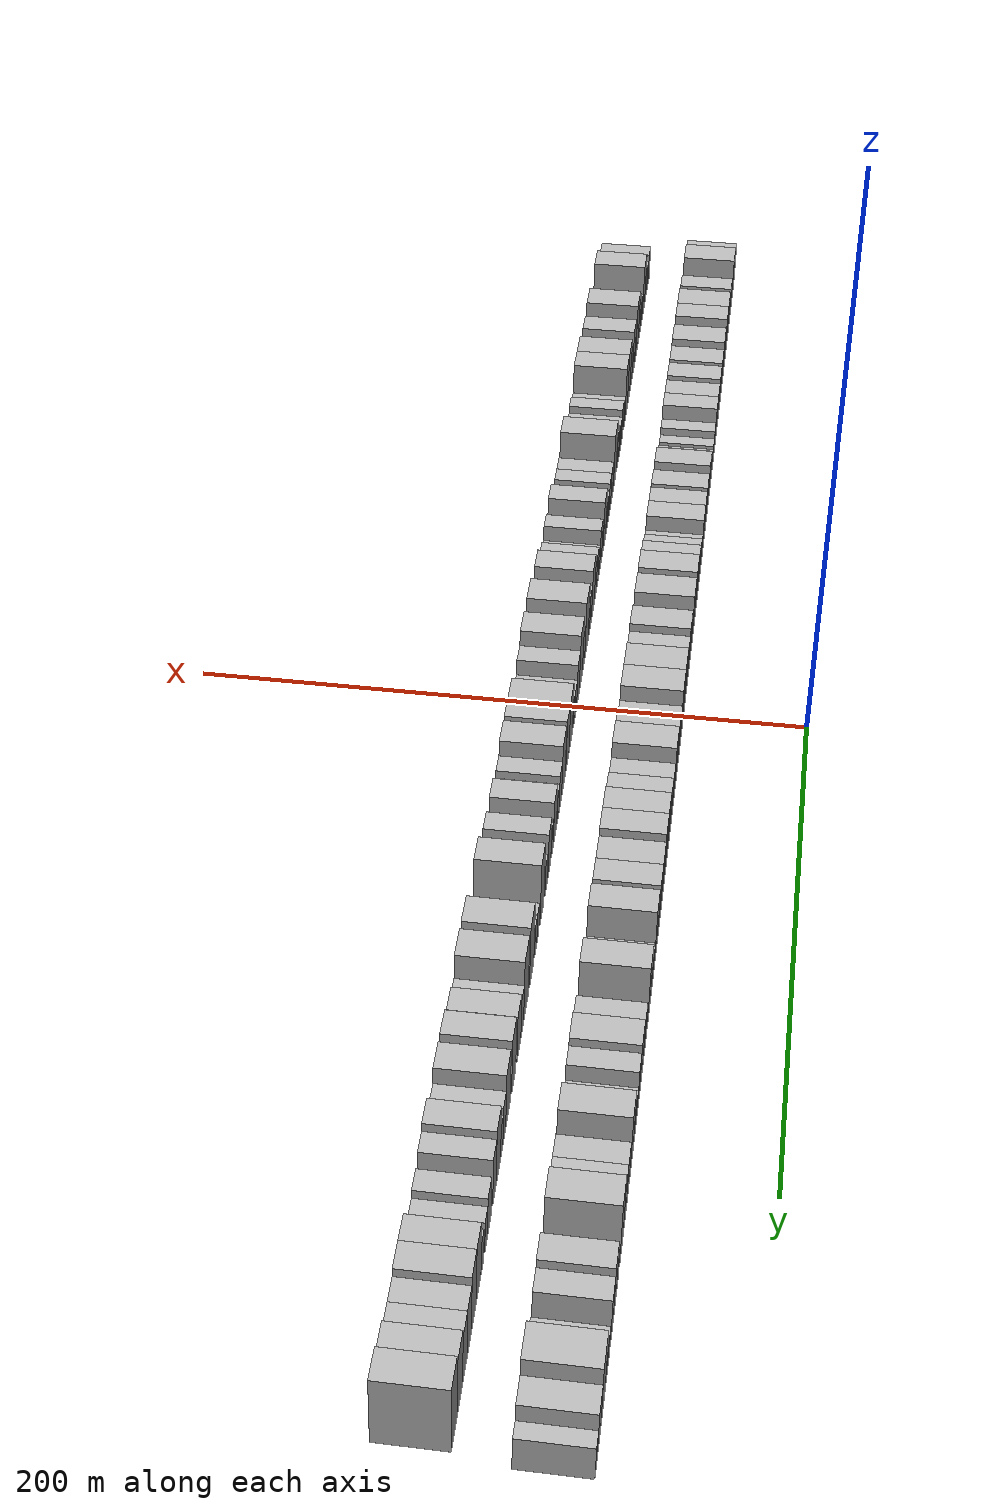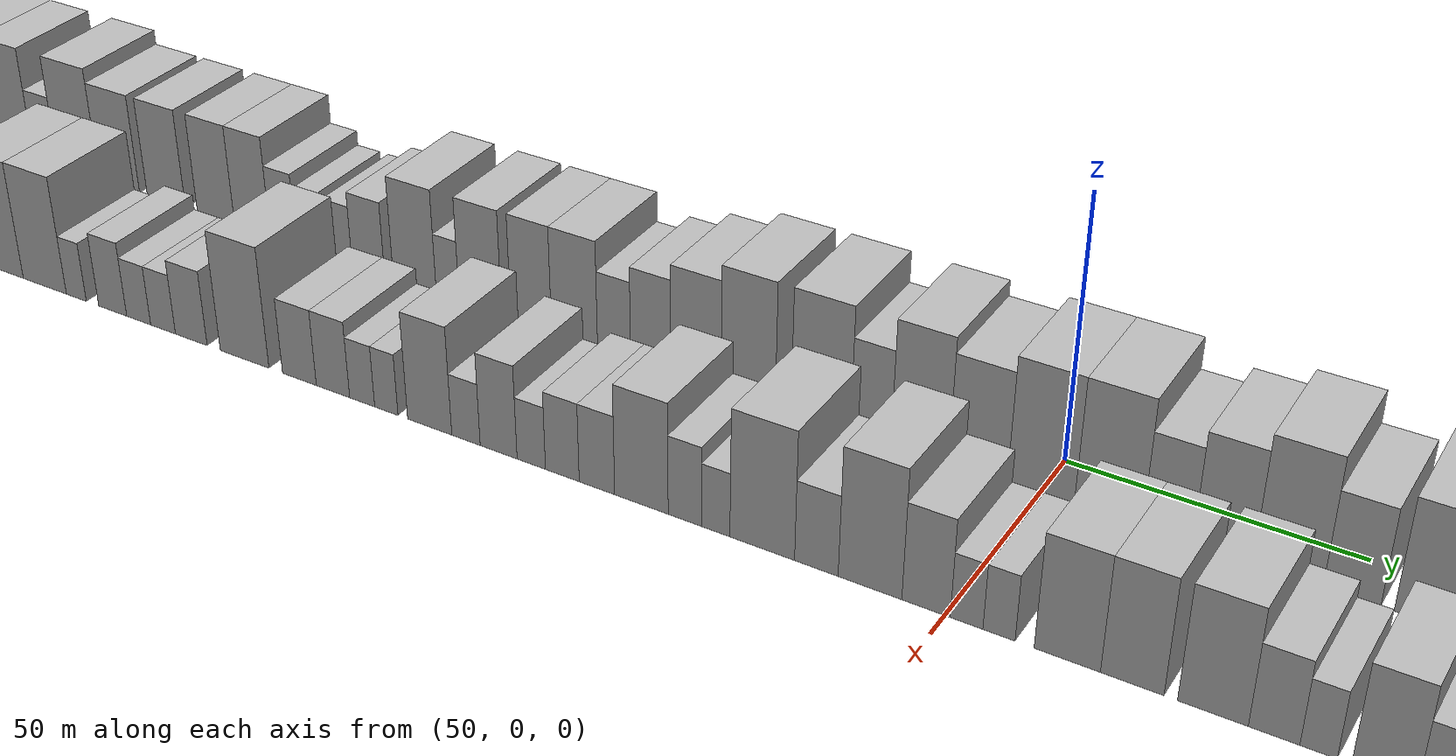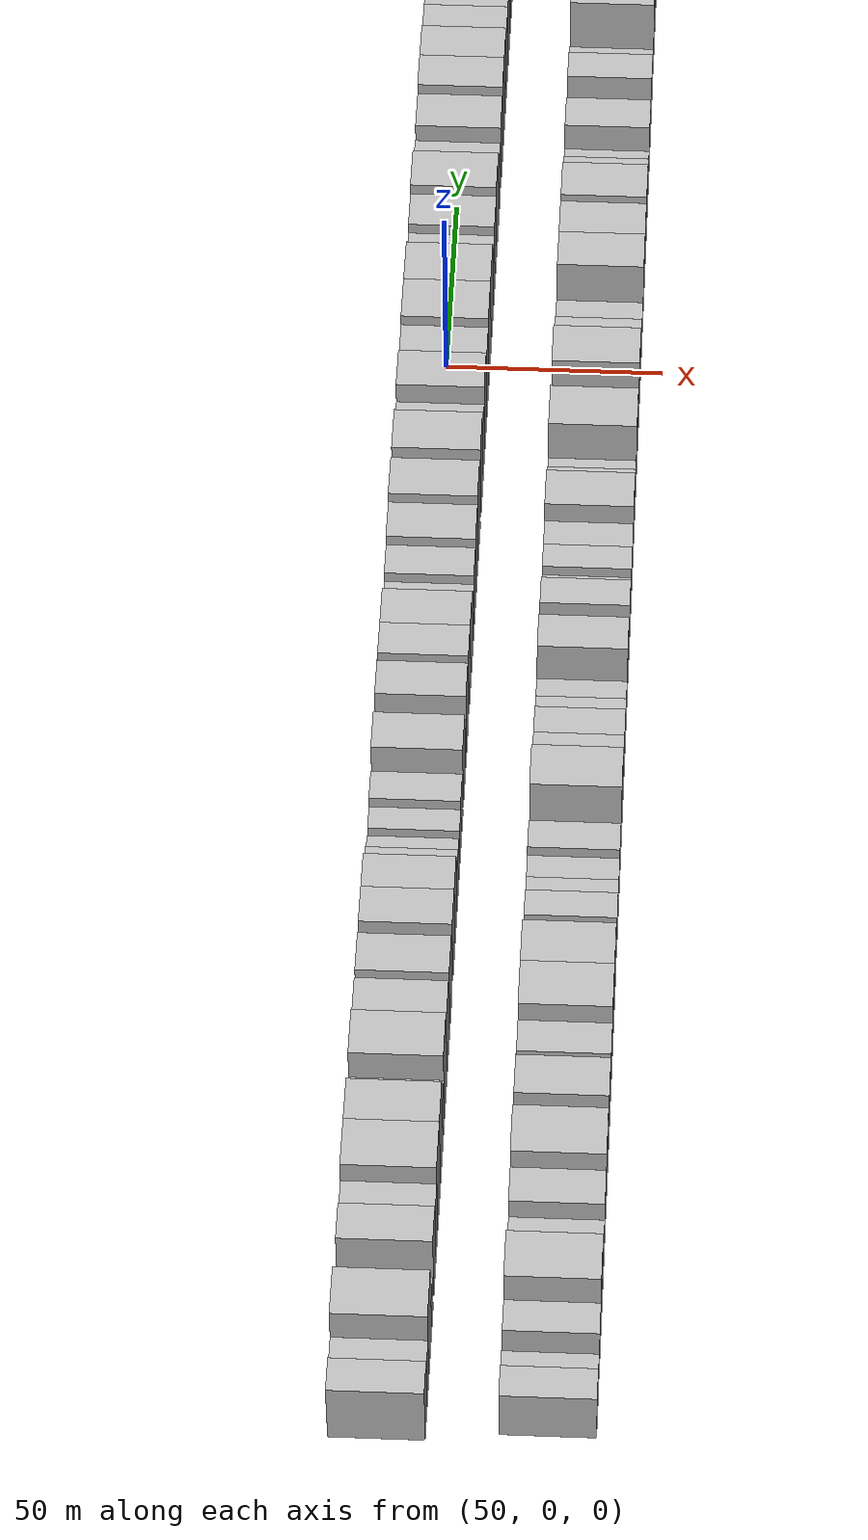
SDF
<sdf version="1.6">
 <world name="default">
  <scene>
   <sky><clouds><speed>12</speed></clouds></sky>
   <ambient>0.4 0.4 0.4 1</ambient>
   <background>0.7 0.7 0.7 1</background>
   <shadows>1</shadows>
  </scene>
  <gravity>0 0 -9.8066</gravity>
  <magnetic_field>6e-06 2.3e-05 -4.2e-05</magnetic_field>
  <physics default="0" name="default_physics" type="ode">
   <ode>
    <solver>
     <type>quick</type>
     <iters>10</iters>
     <sor>1.0</sor>
     <use_dynamic_moi_rescaling>0</use_dynamic_moi_rescaling>
    </solver>
    <constraints>
     <cfm>0</cfm>
     <erp>0.2</erp>
     <contact_max_correcting_vel>100</contact_max_correcting_vel>
     <contact_surface_layer>0.001</contact_surface_layer>
    </constraints>
   </ode>
   <max_step_size>0.004</max_step_size>
   <real_time_factor>1</real_time_factor>
   <real_time_update_rate>250</real_time_update_rate>
  </physics>
  <light name="sun" type="directional">
   <pose>0 0 10 0 0 0</pose>
   <diffuse>0.8 0.8 0.8 1</diffuse>
   <specular>0.2 0.2 0.2 1</specular>
   <attenuation>
    <range>1000</range>
    <constant>0.9</constant>
    <linear>0.01</linear>
    <quadratic>0.001</quadratic>
   </attenuation>
   <direction>-0.5 0.1 -0.9</direction>
  </light>
  <model name="building_1">
   <static>1</static>
   <pose>50.0000 -286.1215 0 0.000000 0.000000 0.000000</pose>
   <link name="link">
    <pose>0 0 9.00 0 0 0</pose>
    <collision name="collision"><geometry><box><size>20.0000 7.7570 18.0000</size></box></geometry></collision>
    <visual name="visual">
     <cast_shadows>0</cast_shadows>
     <geometry><box><size>20.0000 7.7570 18.0000</size></box></geometry>
     <material>
      <script>
       <uri>model://HANNAS_wall/materials/scripts</uri>
       <uri>model://HANNAS_wall/materials/textures</uri>
       <name>vrc/HANNAS_wall</name>
      </script>
     </material>
    </visual>
   </link>
  </model>
  <model name="building_2">
   <static>1</static>
   <pose>50.0000 -278.8270 0 0.000000 0.000000 0.000000</pose>
   <link name="link">
    <pose>0 0 7.50 0 0 0</pose>
    <collision name="collision"><geometry><box><size>20.0000 6.8320 15.0000</size></box></geometry></collision>
    <visual name="visual">
     <cast_shadows>0</cast_shadows>
     <geometry><box><size>20.0000 6.8320 15.0000</size></box></geometry>
     <material>
      <script>
       <uri>model://HANNAS_wall/materials/scripts</uri>
       <uri>model://HANNAS_wall/materials/textures</uri>
       <name>vrc/HANNAS_wall</name>
      </script>
     </material>
    </visual>
   </link>
  </model>
  <model name="building_3">
   <static>1</static>
   <pose>50.0000 -269.7757 0 0.000000 0.000000 0.000000</pose>
   <link name="link">
    <pose>0 0 12.00 0 0 0</pose>
    <collision name="collision"><geometry><box><size>20.0000 11.2707 24.0000</size></box></geometry></collision>
    <visual name="visual">
     <cast_shadows>0</cast_shadows>
     <geometry><box><size>20.0000 11.2707 24.0000</size></box></geometry>
     <material>
      <script>
       <uri>model://HANNAS_wall/materials/scripts</uri>
       <uri>model://HANNAS_wall/materials/textures</uri>
       <name>vrc/HANNAS_wall</name>
      </script>
     </material>
    </visual>
   </link>
  </model>
  <model name="building_4">
   <static>1</static>
   <pose>50.0000 -261.1893 0 0.000000 0.000000 0.000000</pose>
   <link name="link">
    <pose>0 0 6.00 0 0 0</pose>
    <collision name="collision"><geometry><box><size>20.0000 5.9021 12.0000</size></box></geometry></collision>
    <visual name="visual">
     <cast_shadows>0</cast_shadows>
     <geometry><box><size>20.0000 5.9021 12.0000</size></box></geometry>
     <material>
      <script>
       <uri>model://HANNAS_wall/materials/scripts</uri>
       <uri>model://HANNAS_wall/materials/textures</uri>
       <name>vrc/HANNAS_wall</name>
      </script>
     </material>
    </visual>
   </link>
  </model>
  <model name="building_5">
   <static>1</static>
   <pose>50.0000 -250.8855 0 0.000000 0.000000 0.000000</pose>
   <link name="link">
    <pose>0 0 10.50 0 0 0</pose>
    <collision name="collision"><geometry><box><size>20.0000 8.7054 21.0000</size></box></geometry></collision>
    <visual name="visual">
     <cast_shadows>0</cast_shadows>
     <geometry><box><size>20.0000 8.7054 21.0000</size></box></geometry>
     <material>
      <script>
       <uri>model://HANNAS_wall/materials/scripts</uri>
       <uri>model://HANNAS_wall/materials/textures</uri>
       <name>vrc/HANNAS_wall</name>
      </script>
     </material>
    </visual>
   </link>
  </model>
  <model name="building_6">
   <static>1</static>
   <pose>50.0000 -242.7980 0 0.000000 0.000000 0.000000</pose>
   <link name="link">
    <pose>0 0 9.00 0 0 0</pose>
    <collision name="collision"><geometry><box><size>20.0000 7.4695 18.0000</size></box></geometry></collision>
    <visual name="visual">
     <cast_shadows>0</cast_shadows>
     <geometry><box><size>20.0000 7.4695 18.0000</size></box></geometry>
     <material>
      <script>
       <uri>model://HANNAS_wall/materials/scripts</uri>
       <uri>model://HANNAS_wall/materials/textures</uri>
       <name>vrc/HANNAS_wall</name>
      </script>
     </material>
    </visual>
   </link>
  </model>
  <model name="building_7">
   <static>1</static>
   <pose>50.0000 -233.3170 0 0.000000 0.000000 0.000000</pose>
   <link name="link">
    <pose>0 0 12.00 0 0 0</pose>
    <collision name="collision"><geometry><box><size>20.0000 11.4925 24.0000</size></box></geometry></collision>
    <visual name="visual">
     <cast_shadows>0</cast_shadows>
     <geometry><box><size>20.0000 11.4925 24.0000</size></box></geometry>
     <material>
      <script>
       <uri>model://HANNAS_wall/materials/scripts</uri>
       <uri>model://HANNAS_wall/materials/textures</uri>
       <name>vrc/HANNAS_wall</name>
      </script>
     </material>
    </visual>
   </link>
  </model>
  <model name="building_8">
   <static>1</static>
   <pose>50.0000 -222.5030 0 0.000000 0.000000 0.000000</pose>
   <link name="link">
    <pose>0 0 12.00 0 0 0</pose>
    <collision name="collision"><geometry><box><size>20.0000 10.1356 24.0000</size></box></geometry></collision>
    <visual name="visual">
     <cast_shadows>0</cast_shadows>
     <geometry><box><size>20.0000 10.1356 24.0000</size></box></geometry>
     <material>
      <script>
       <uri>model://HANNAS_wall/materials/scripts</uri>
       <uri>model://HANNAS_wall/materials/textures</uri>
       <name>vrc/HANNAS_wall</name>
      </script>
     </material>
    </visual>
   </link>
  </model>
  <model name="building_9">
   <static>1</static>
   <pose>50.0000 -214.2020 0 0.000000 0.000000 0.000000</pose>
   <link name="link">
    <pose>0 0 7.50 0 0 0</pose>
    <collision name="collision"><geometry><box><size>20.0000 6.4662 15.0000</size></box></geometry></collision>
    <visual name="visual">
     <cast_shadows>0</cast_shadows>
     <geometry><box><size>20.0000 6.4662 15.0000</size></box></geometry>
     <material>
      <script>
       <uri>model://HANNAS_wall/materials/scripts</uri>
       <uri>model://HANNAS_wall/materials/textures</uri>
       <name>vrc/HANNAS_wall</name>
      </script>
     </material>
    </visual>
   </link>
  </model>
  <model name="building_10">
   <static>1</static>
   <pose>50.0000 -205.4233 0 0.000000 0.000000 0.000000</pose>
   <link name="link">
    <pose>0 0 12.00 0 0 0</pose>
    <collision name="collision"><geometry><box><size>20.0000 11.0913 24.0000</size></box></geometry></collision>
    <visual name="visual">
     <cast_shadows>0</cast_shadows>
     <geometry><box><size>20.0000 11.0913 24.0000</size></box></geometry>
     <material>
      <script>
       <uri>model://HANNAS_wall/materials/scripts</uri>
       <uri>model://HANNAS_wall/materials/textures</uri>
       <name>vrc/HANNAS_wall</name>
      </script>
     </material>
    </visual>
   </link>
  </model>
  <model name="building_11">
   <static>1</static>
   <pose>50.0000 -194.6759 0 0.000000 0.000000 0.000000</pose>
   <link name="link">
    <pose>0 0 10.50 0 0 0</pose>
    <collision name="collision"><geometry><box><size>20.0000 10.4035 21.0000</size></box></geometry></collision>
    <visual name="visual">
     <cast_shadows>0</cast_shadows>
     <geometry><box><size>20.0000 10.4035 21.0000</size></box></geometry>
     <material>
      <script>
       <uri>model://HANNAS_wall/materials/scripts</uri>
       <uri>model://HANNAS_wall/materials/textures</uri>
       <name>vrc/HANNAS_wall</name>
      </script>
     </material>
    </visual>
   </link>
  </model>
  <model name="building_12">
   <static>1</static>
   <pose>50.0000 -182.6092 0 0.000000 0.000000 0.000000</pose>
   <link name="link">
    <pose>0 0 10.50 0 0 0</pose>
    <collision name="collision"><geometry><box><size>20.0000 9.7299 21.0000</size></box></geometry></collision>
    <visual name="visual">
     <cast_shadows>0</cast_shadows>
     <geometry><box><size>20.0000 9.7299 21.0000</size></box></geometry>
     <material>
      <script>
       <uri>model://HANNAS_wall/materials/scripts</uri>
       <uri>model://HANNAS_wall/materials/textures</uri>
       <name>vrc/HANNAS_wall</name>
      </script>
     </material>
    </visual>
   </link>
  </model>
  <model name="building_13">
   <static>1</static>
   <pose>50.0000 -170.1240 0 0.000000 0.000000 0.000000</pose>
   <link name="link">
    <pose>0 0 10.50 0 0 0</pose>
    <collision name="collision"><geometry><box><size>20.0000 9.2405 21.0000</size></box></geometry></collision>
    <visual name="visual">
     <cast_shadows>0</cast_shadows>
     <geometry><box><size>20.0000 9.2405 21.0000</size></box></geometry>
     <material>
      <script>
       <uri>model://HANNAS_wall/materials/scripts</uri>
       <uri>model://HANNAS_wall/materials/textures</uri>
       <name>vrc/HANNAS_wall</name>
      </script>
     </material>
    </visual>
   </link>
  </model>
  <model name="building_14">
   <static>1</static>
   <pose>50.0000 -161.1200 0 0.000000 0.000000 0.000000</pose>
   <link name="link">
    <pose>0 0 10.50 0 0 0</pose>
    <collision name="collision"><geometry><box><size>20.0000 8.7677 21.0000</size></box></geometry></collision>
    <visual name="visual">
     <cast_shadows>0</cast_shadows>
     <geometry><box><size>20.0000 8.7677 21.0000</size></box></geometry>
     <material>
      <script>
       <uri>model://HANNAS_wall/materials/scripts</uri>
       <uri>model://HANNAS_wall/materials/textures</uri>
       <name>vrc/HANNAS_wall</name>
      </script>
     </material>
    </visual>
   </link>
  </model>
  <model name="building_15">
   <static>1</static>
   <pose>50.0000 -153.6096 0 0.000000 0.000000 0.000000</pose>
   <link name="link">
    <pose>0 0 7.50 0 0 0</pose>
    <collision name="collision"><geometry><box><size>20.0000 6.2531 15.0000</size></box></geometry></collision>
    <visual name="visual">
     <cast_shadows>0</cast_shadows>
     <geometry><box><size>20.0000 6.2531 15.0000</size></box></geometry>
     <material>
      <script>
       <uri>model://HANNAS_wall/materials/scripts</uri>
       <uri>model://HANNAS_wall/materials/textures</uri>
       <name>vrc/HANNAS_wall</name>
      </script>
     </material>
    </visual>
   </link>
  </model>
  <model name="building_16">
   <static>1</static>
   <pose>50.0000 -147.8649 0 0.000000 0.000000 0.000000</pose>
   <link name="link">
    <pose>0 0 6.00 0 0 0</pose>
    <collision name="collision"><geometry><box><size>20.0000 5.2362 12.0000</size></box></geometry></collision>
    <visual name="visual">
     <cast_shadows>0</cast_shadows>
     <geometry><box><size>20.0000 5.2362 12.0000</size></box></geometry>
     <material>
      <script>
       <uri>model://HANNAS_wall/materials/scripts</uri>
       <uri>model://HANNAS_wall/materials/textures</uri>
       <name>vrc/HANNAS_wall</name>
      </script>
     </material>
    </visual>
   </link>
  </model>
  <model name="building_17">
   <static>1</static>
   <pose>50.0000 -140.3186 0 0.000000 0.000000 0.000000</pose>
   <link name="link">
    <pose>0 0 6.00 0 0 0</pose>
    <collision name="collision"><geometry><box><size>20.0000 5.8565 12.0000</size></box></geometry></collision>
    <visual name="visual">
     <cast_shadows>0</cast_shadows>
     <geometry><box><size>20.0000 5.8565 12.0000</size></box></geometry>
     <material>
      <script>
       <uri>model://HANNAS_wall/materials/scripts</uri>
       <uri>model://HANNAS_wall/materials/textures</uri>
       <name>vrc/HANNAS_wall</name>
      </script>
     </material>
    </visual>
   </link>
  </model>
  <model name="building_18">
   <static>1</static>
   <pose>50.0000 -133.6566 0 0.000000 0.000000 0.000000</pose>
   <link name="link">
    <pose>0 0 7.50 0 0 0</pose>
    <collision name="collision"><geometry><box><size>20.0000 7.4675 15.0000</size></box></geometry></collision>
    <visual name="visual">
     <cast_shadows>0</cast_shadows>
     <geometry><box><size>20.0000 7.4675 15.0000</size></box></geometry>
     <material>
      <script>
       <uri>model://HANNAS_wall/materials/scripts</uri>
       <uri>model://HANNAS_wall/materials/textures</uri>
       <name>vrc/HANNAS_wall</name>
      </script>
     </material>
    </visual>
   </link>
  </model>
  <model name="building_19">
   <static>1</static>
   <pose>50.0000 -123.0752 0 0.000000 0.000000 0.000000</pose>
   <link name="link">
    <pose>0 0 10.50 0 0 0</pose>
    <collision name="collision"><geometry><box><size>20.0000 9.6954 21.0000</size></box></geometry></collision>
    <visual name="visual">
     <cast_shadows>0</cast_shadows>
     <geometry><box><size>20.0000 9.6954 21.0000</size></box></geometry>
     <material>
      <script>
       <uri>model://HANNAS_wall/materials/scripts</uri>
       <uri>model://HANNAS_wall/materials/textures</uri>
       <name>vrc/HANNAS_wall</name>
      </script>
     </material>
    </visual>
   </link>
  </model>
  <model name="building_20">
   <static>1</static>
   <pose>50.0000 -115.6815 0 0.000000 0.000000 0.000000</pose>
   <link name="link">
    <pose>0 0 6.00 0 0 0</pose>
    <collision name="collision"><geometry><box><size>20.0000 5.0921 12.0000</size></box></geometry></collision>
    <visual name="visual">
     <cast_shadows>0</cast_shadows>
     <geometry><box><size>20.0000 5.0921 12.0000</size></box></geometry>
     <material>
      <script>
       <uri>model://HANNAS_wall/materials/scripts</uri>
       <uri>model://HANNAS_wall/materials/textures</uri>
       <name>vrc/HANNAS_wall</name>
      </script>
     </material>
    </visual>
   </link>
  </model>
  <model name="building_21">
   <static>1</static>
   <pose>50.0000 -108.4756 0 0.000000 0.000000 0.000000</pose>
   <link name="link">
    <pose>0 0 10.50 0 0 0</pose>
    <collision name="collision"><geometry><box><size>20.0000 9.3197 21.0000</size></box></geometry></collision>
    <visual name="visual">
     <cast_shadows>0</cast_shadows>
     <geometry><box><size>20.0000 9.3197 21.0000</size></box></geometry>
     <material>
      <script>
       <uri>model://HANNAS_wall/materials/scripts</uri>
       <uri>model://HANNAS_wall/materials/textures</uri>
       <name>vrc/HANNAS_wall</name>
      </script>
     </material>
    </visual>
   </link>
  </model>
  <model name="building_22">
   <static>1</static>
   <pose>50.0000 -97.4793 0 0.000000 0.000000 0.000000</pose>
   <link name="link">
    <pose>0 0 10.50 0 0 0</pose>
    <collision name="collision"><geometry><box><size>20.0000 8.6728 21.0000</size></box></geometry></collision>
    <visual name="visual">
     <cast_shadows>0</cast_shadows>
     <geometry><box><size>20.0000 8.6728 21.0000</size></box></geometry>
     <material>
      <script>
       <uri>model://HANNAS_wall/materials/scripts</uri>
       <uri>model://HANNAS_wall/materials/textures</uri>
       <name>vrc/HANNAS_wall</name>
      </script>
     </material>
    </visual>
   </link>
  </model>
  <model name="building_23">
   <static>1</static>
   <pose>50.0000 -88.3276 0 0.000000 0.000000 0.000000</pose>
   <link name="link">
    <pose>0 0 10.50 0 0 0</pose>
    <collision name="collision"><geometry><box><size>20.0000 9.6306 21.0000</size></box></geometry></collision>
    <visual name="visual">
     <cast_shadows>0</cast_shadows>
     <geometry><box><size>20.0000 9.6306 21.0000</size></box></geometry>
     <material>
      <script>
       <uri>model://HANNAS_wall/materials/scripts</uri>
       <uri>model://HANNAS_wall/materials/textures</uri>
       <name>vrc/HANNAS_wall</name>
      </script>
     </material>
    </visual>
   </link>
  </model>
  <model name="building_24">
   <static>1</static>
   <pose>50.0000 -80.1042 0 0.000000 0.000000 0.000000</pose>
   <link name="link">
    <pose>0 0 7.50 0 0 0</pose>
    <collision name="collision"><geometry><box><size>20.0000 6.8162 15.0000</size></box></geometry></collision>
    <visual name="visual">
     <cast_shadows>0</cast_shadows>
     <geometry><box><size>20.0000 6.8162 15.0000</size></box></geometry>
     <material>
      <script>
       <uri>model://HANNAS_wall/materials/scripts</uri>
       <uri>model://HANNAS_wall/materials/textures</uri>
       <name>vrc/HANNAS_wall</name>
      </script>
     </material>
    </visual>
   </link>
  </model>
  <model name="building_25">
   <static>1</static>
   <pose>50.0000 -72.6265 0 0.000000 0.000000 0.000000</pose>
   <link name="link">
    <pose>0 0 9.00 0 0 0</pose>
    <collision name="collision"><geometry><box><size>20.0000 8.1390 18.0000</size></box></geometry></collision>
    <visual name="visual">
     <cast_shadows>0</cast_shadows>
     <geometry><box><size>20.0000 8.1390 18.0000</size></box></geometry>
     <material>
      <script>
       <uri>model://HANNAS_wall/materials/scripts</uri>
       <uri>model://HANNAS_wall/materials/textures</uri>
       <name>vrc/HANNAS_wall</name>
      </script>
     </material>
    </visual>
   </link>
  </model>
  <model name="building_26">
   <static>1</static>
   <pose>50.0000 -63.5773 0 0.000000 0.000000 0.000000</pose>
   <link name="link">
    <pose>0 0 10.50 0 0 0</pose>
    <collision name="collision"><geometry><box><size>20.0000 9.9593 21.0000</size></box></geometry></collision>
    <visual name="visual">
     <cast_shadows>0</cast_shadows>
     <geometry><box><size>20.0000 9.9593 21.0000</size></box></geometry>
     <material>
      <script>
       <uri>model://HANNAS_wall/materials/scripts</uri>
       <uri>model://HANNAS_wall/materials/textures</uri>
       <name>vrc/HANNAS_wall</name>
      </script>
     </material>
    </visual>
   </link>
  </model>
  <model name="building_27">
   <static>1</static>
   <pose>50.0000 -53.3399 0 0.000000 0.000000 0.000000</pose>
   <link name="link">
    <pose>0 0 12.00 0 0 0</pose>
    <collision name="collision"><geometry><box><size>20.0000 10.5155 24.0000</size></box></geometry></collision>
    <visual name="visual">
     <cast_shadows>0</cast_shadows>
     <geometry><box><size>20.0000 10.5155 24.0000</size></box></geometry>
     <material>
      <script>
       <uri>model://HANNAS_wall/materials/scripts</uri>
       <uri>model://HANNAS_wall/materials/textures</uri>
       <name>vrc/HANNAS_wall</name>
      </script>
     </material>
    </visual>
   </link>
  </model>
  <model name="building_28">
   <static>1</static>
   <pose>50.0000 -39.4996 0 0.000000 0.000000 0.000000</pose>
   <link name="link">
    <pose>0 0 12.00 0 0 0</pose>
    <collision name="collision"><geometry><box><size>20.0000 11.1651 24.0000</size></box></geometry></collision>
    <visual name="visual">
     <cast_shadows>0</cast_shadows>
     <geometry><box><size>20.0000 11.1651 24.0000</size></box></geometry>
     <material>
      <script>
       <uri>model://HANNAS_wall/materials/scripts</uri>
       <uri>model://HANNAS_wall/materials/textures</uri>
       <name>vrc/HANNAS_wall</name>
      </script>
     </material>
    </visual>
   </link>
  </model>
  <model name="building_29">
   <static>1</static>
   <pose>50.0000 -30.1853 0 0.000000 0.000000 0.000000</pose>
   <link name="link">
    <pose>0 0 9.00 0 0 0</pose>
    <collision name="collision"><geometry><box><size>20.0000 7.4636 18.0000</size></box></geometry></collision>
    <visual name="visual">
     <cast_shadows>0</cast_shadows>
     <geometry><box><size>20.0000 7.4636 18.0000</size></box></geometry>
     <material>
      <script>
       <uri>model://HANNAS_wall/materials/scripts</uri>
       <uri>model://HANNAS_wall/materials/textures</uri>
       <name>vrc/HANNAS_wall</name>
      </script>
     </material>
    </visual>
   </link>
  </model>
  <model name="building_30">
   <static>1</static>
   <pose>50.0000 -21.2771 0 0.000000 0.000000 0.000000</pose>
   <link name="link">
    <pose>0 0 12.00 0 0 0</pose>
    <collision name="collision"><geometry><box><size>20.0000 10.3528 24.0000</size></box></geometry></collision>
    <visual name="visual">
     <cast_shadows>0</cast_shadows>
     <geometry><box><size>20.0000 10.3528 24.0000</size></box></geometry>
     <material>
      <script>
       <uri>model://HANNAS_wall/materials/scripts</uri>
       <uri>model://HANNAS_wall/materials/textures</uri>
       <name>vrc/HANNAS_wall</name>
      </script>
     </material>
    </visual>
   </link>
  </model>
  <model name="building_31">
   <static>1</static>
   <pose>50.0000 -10.9380 0 0.000000 0.000000 0.000000</pose>
   <link name="link">
    <pose>0 0 10.50 0 0 0</pose>
    <collision name="collision"><geometry><box><size>20.0000 10.3253 21.0000</size></box></geometry></collision>
    <visual name="visual">
     <cast_shadows>0</cast_shadows>
     <geometry><box><size>20.0000 10.3253 21.0000</size></box></geometry>
     <material>
      <script>
       <uri>model://HANNAS_wall/materials/scripts</uri>
       <uri>model://HANNAS_wall/materials/textures</uri>
       <name>vrc/HANNAS_wall</name>
      </script>
     </material>
    </visual>
   </link>
  </model>
  <model name="building_32">
   <static>1</static>
   <pose>50.0000 -0.0336 0 0.000000 0.000000 0.000000</pose>
   <link name="link">
    <pose>0 0 12.00 0 0 0</pose>
    <collision name="collision"><geometry><box><size>20.0000 11.4835 24.0000</size></box></geometry></collision>
    <visual name="visual">
     <cast_shadows>0</cast_shadows>
     <geometry><box><size>20.0000 11.4835 24.0000</size></box></geometry>
     <material>
      <script>
       <uri>model://HANNAS_wall/materials/scripts</uri>
       <uri>model://HANNAS_wall/materials/textures</uri>
       <name>vrc/HANNAS_wall</name>
      </script>
     </material>
    </visual>
   </link>
  </model>
  <model name="building_33">
   <static>1</static>
   <pose>50.0000 11.3672 0 0.000000 0.000000 0.000000</pose>
   <link name="link">
    <pose>0 0 12.00 0 0 0</pose>
    <collision name="collision"><geometry><box><size>20.0000 11.3181 24.0000</size></box></geometry></collision>
    <visual name="visual">
     <cast_shadows>0</cast_shadows>
     <geometry><box><size>20.0000 11.3181 24.0000</size></box></geometry>
     <material>
      <script>
       <uri>model://HANNAS_wall/materials/scripts</uri>
       <uri>model://HANNAS_wall/materials/textures</uri>
       <name>vrc/HANNAS_wall</name>
      </script>
     </material>
    </visual>
   </link>
  </model>
  <model name="building_34">
   <static>1</static>
   <pose>50.0000 21.1201 0 0.000000 0.000000 0.000000</pose>
   <link name="link">
    <pose>0 0 9.00 0 0 0</pose>
    <collision name="collision"><geometry><box><size>20.0000 8.1878 18.0000</size></box></geometry></collision>
    <visual name="visual">
     <cast_shadows>0</cast_shadows>
     <geometry><box><size>20.0000 8.1878 18.0000</size></box></geometry>
     <material>
      <script>
       <uri>model://HANNAS_wall/materials/scripts</uri>
       <uri>model://HANNAS_wall/materials/textures</uri>
       <name>vrc/HANNAS_wall</name>
      </script>
     </material>
    </visual>
   </link>
  </model>
  <model name="building_35">
   <static>1</static>
   <pose>50.0000 30.0102 0 0.000000 0.000000 0.000000</pose>
   <link name="link">
    <pose>0 0 10.50 0 0 0</pose>
    <collision name="collision"><geometry><box><size>20.0000 9.5924 21.0000</size></box></geometry></collision>
    <visual name="visual">
     <cast_shadows>0</cast_shadows>
     <geometry><box><size>20.0000 9.5924 21.0000</size></box></geometry>
     <material>
      <script>
       <uri>model://HANNAS_wall/materials/scripts</uri>
       <uri>model://HANNAS_wall/materials/textures</uri>
       <name>vrc/HANNAS_wall</name>
      </script>
     </material>
    </visual>
   </link>
  </model>
  <model name="building_36">
   <static>1</static>
   <pose>50.0000 40.2652 0 0.000000 0.000000 0.000000</pose>
   <link name="link">
    <pose>0 0 12.00 0 0 0</pose>
    <collision name="collision"><geometry><box><size>20.0000 10.9175 24.0000</size></box></geometry></collision>
    <visual name="visual">
     <cast_shadows>0</cast_shadows>
     <geometry><box><size>20.0000 10.9175 24.0000</size></box></geometry>
     <material>
      <script>
       <uri>model://HANNAS_wall/materials/scripts</uri>
       <uri>model://HANNAS_wall/materials/textures</uri>
       <name>vrc/HANNAS_wall</name>
      </script>
     </material>
    </visual>
   </link>
  </model>
  <model name="building_37">
   <static>1</static>
   <pose>50.0000 50.0913 0 0.000000 0.000000 0.000000</pose>
   <link name="link">
    <pose>0 0 9.00 0 0 0</pose>
    <collision name="collision"><geometry><box><size>20.0000 8.7346 18.0000</size></box></geometry></collision>
    <visual name="visual">
     <cast_shadows>0</cast_shadows>
     <geometry><box><size>20.0000 8.7346 18.0000</size></box></geometry>
     <material>
      <script>
       <uri>model://HANNAS_wall/materials/scripts</uri>
       <uri>model://HANNAS_wall/materials/textures</uri>
       <name>vrc/HANNAS_wall</name>
      </script>
     </material>
    </visual>
   </link>
  </model>
  <model name="building_38">
   <static>1</static>
   <pose>50.0000 61.6384 0 0.000000 0.000000 0.000000</pose>
   <link name="link">
    <pose>0 0 10.50 0 0 0</pose>
    <collision name="collision"><geometry><box><size>20.0000 10.3596 21.0000</size></box></geometry></collision>
    <visual name="visual">
     <cast_shadows>0</cast_shadows>
     <geometry><box><size>20.0000 10.3596 21.0000</size></box></geometry>
     <material>
      <script>
       <uri>model://HANNAS_wall/materials/scripts</uri>
       <uri>model://HANNAS_wall/materials/textures</uri>
       <name>vrc/HANNAS_wall</name>
      </script>
     </material>
    </visual>
   </link>
  </model>
  <model name="building_39">
   <static>1</static>
   <pose>50.0000 71.6569 0 0.000000 0.000000 0.000000</pose>
   <link name="link">
    <pose>0 0 12.00 0 0 0</pose>
    <collision name="collision"><geometry><box><size>20.0000 9.6773 24.0000</size></box></geometry></collision>
    <visual name="visual">
     <cast_shadows>0</cast_shadows>
     <geometry><box><size>20.0000 9.6773 24.0000</size></box></geometry>
     <material>
      <script>
       <uri>model://HANNAS_wall/materials/scripts</uri>
       <uri>model://HANNAS_wall/materials/textures</uri>
       <name>vrc/HANNAS_wall</name>
      </script>
     </material>
    </visual>
   </link>
  </model>
  <model name="building_40">
   <static>1</static>
   <pose>50.0000 81.2991 0 0.000000 0.000000 0.000000</pose>
   <link name="link">
    <pose>0 0 12.00 0 0 0</pose>
    <collision name="collision"><geometry><box><size>20.0000 9.6071 24.0000</size></box></geometry></collision>
    <visual name="visual">
     <cast_shadows>0</cast_shadows>
     <geometry><box><size>20.0000 9.6071 24.0000</size></box></geometry>
     <material>
      <script>
       <uri>model://HANNAS_wall/materials/scripts</uri>
       <uri>model://HANNAS_wall/materials/textures</uri>
       <name>vrc/HANNAS_wall</name>
      </script>
     </material>
    </visual>
   </link>
  </model>
  <model name="building_41">
   <static>1</static>
   <pose>50.0000 91.0452 0 0.000000 0.000000 0.000000</pose>
   <link name="link">
    <pose>0 0 10.50 0 0 0</pose>
    <collision name="collision"><geometry><box><size>20.0000 9.8851 21.0000</size></box></geometry></collision>
    <visual name="visual">
     <cast_shadows>0</cast_shadows>
     <geometry><box><size>20.0000 9.8851 21.0000</size></box></geometry>
     <material>
      <script>
       <uri>model://HANNAS_wall/materials/scripts</uri>
       <uri>model://HANNAS_wall/materials/textures</uri>
       <name>vrc/HANNAS_wall</name>
      </script>
     </material>
    </visual>
   </link>
  </model>
  <model name="building_42">
   <static>1</static>
   <pose>50.0000 100.6910 0 0.000000 0.000000 0.000000</pose>
   <link name="link">
    <pose>0 0 10.50 0 0 0</pose>
    <collision name="collision"><geometry><box><size>20.0000 9.4066 21.0000</size></box></geometry></collision>
    <visual name="visual">
     <cast_shadows>0</cast_shadows>
     <geometry><box><size>20.0000 9.4066 21.0000</size></box></geometry>
     <material>
      <script>
       <uri>model://HANNAS_wall/materials/scripts</uri>
       <uri>model://HANNAS_wall/materials/textures</uri>
       <name>vrc/HANNAS_wall</name>
      </script>
     </material>
    </visual>
   </link>
  </model>
  <model name="building_43">
   <static>1</static>
   <pose>50.0000 107.8658 0 0.000000 0.000000 0.000000</pose>
   <link name="link">
    <pose>0 0 6.00 0 0 0</pose>
    <collision name="collision"><geometry><box><size>20.0000 4.9430 12.0000</size></box></geometry></collision>
    <visual name="visual">
     <cast_shadows>0</cast_shadows>
     <geometry><box><size>20.0000 4.9430 12.0000</size></box></geometry>
     <material>
      <script>
       <uri>model://HANNAS_wall/materials/scripts</uri>
       <uri>model://HANNAS_wall/materials/textures</uri>
       <name>vrc/HANNAS_wall</name>
      </script>
     </material>
    </visual>
   </link>
  </model>
  <model name="building_44">
   <static>1</static>
   <pose>50.0000 115.1878 0 0.000000 0.000000 0.000000</pose>
   <link name="link">
    <pose>0 0 12.00 0 0 0</pose>
    <collision name="collision"><geometry><box><size>20.0000 9.7011 24.0000</size></box></geometry></collision>
    <visual name="visual">
     <cast_shadows>0</cast_shadows>
     <geometry><box><size>20.0000 9.7011 24.0000</size></box></geometry>
     <material>
      <script>
       <uri>model://HANNAS_wall/materials/scripts</uri>
       <uri>model://HANNAS_wall/materials/textures</uri>
       <name>vrc/HANNAS_wall</name>
      </script>
     </material>
    </visual>
   </link>
  </model>
  <model name="building_45">
   <static>1</static>
   <pose>50.0000 123.0309 0 0.000000 0.000000 0.000000</pose>
   <link name="link">
    <pose>0 0 6.00 0 0 0</pose>
    <collision name="collision"><geometry><box><size>20.0000 5.9852 12.0000</size></box></geometry></collision>
    <visual name="visual">
     <cast_shadows>0</cast_shadows>
     <geometry><box><size>20.0000 5.9852 12.0000</size></box></geometry>
     <material>
      <script>
       <uri>model://HANNAS_wall/materials/scripts</uri>
       <uri>model://HANNAS_wall/materials/textures</uri>
       <name>vrc/HANNAS_wall</name>
      </script>
     </material>
    </visual>
   </link>
  </model>
  <model name="building_46">
   <static>1</static>
   <pose>50.0000 130.6669 0 0.000000 0.000000 0.000000</pose>
   <link name="link">
    <pose>0 0 6.00 0 0 0</pose>
    <collision name="collision"><geometry><box><size>20.0000 5.2868 12.0000</size></box></geometry></collision>
    <visual name="visual">
     <cast_shadows>0</cast_shadows>
     <geometry><box><size>20.0000 5.2868 12.0000</size></box></geometry>
     <material>
      <script>
       <uri>model://HANNAS_wall/materials/scripts</uri>
       <uri>model://HANNAS_wall/materials/textures</uri>
       <name>vrc/HANNAS_wall</name>
      </script>
     </material>
    </visual>
   </link>
  </model>
  <model name="building_47">
   <static>1</static>
   <pose>50.0000 138.2354 0 0.000000 0.000000 0.000000</pose>
   <link name="link">
    <pose>0 0 12.00 0 0 0</pose>
    <collision name="collision"><geometry><box><size>20.0000 9.8501 24.0000</size></box></geometry></collision>
    <visual name="visual">
     <cast_shadows>0</cast_shadows>
     <geometry><box><size>20.0000 9.8501 24.0000</size></box></geometry>
     <material>
      <script>
       <uri>model://HANNAS_wall/materials/scripts</uri>
       <uri>model://HANNAS_wall/materials/textures</uri>
       <name>vrc/HANNAS_wall</name>
      </script>
     </material>
    </visual>
   </link>
  </model>
  <model name="building_48">
   <static>1</static>
   <pose>50.0000 147.7695 0 0.000000 0.000000 0.000000</pose>
   <link name="link">
    <pose>0 0 6.00 0 0 0</pose>
    <collision name="collision"><geometry><box><size>20.0000 5.2181 12.0000</size></box></geometry></collision>
    <visual name="visual">
     <cast_shadows>0</cast_shadows>
     <geometry><box><size>20.0000 5.2181 12.0000</size></box></geometry>
     <material>
      <script>
       <uri>model://HANNAS_wall/materials/scripts</uri>
       <uri>model://HANNAS_wall/materials/textures</uri>
       <name>vrc/HANNAS_wall</name>
      </script>
     </material>
    </visual>
   </link>
  </model>
  <model name="building_49">
   <static>1</static>
   <pose>50.0000 154.1735 0 0.000000 0.000000 0.000000</pose>
   <link name="link">
    <pose>0 0 9.00 0 0 0</pose>
    <collision name="collision"><geometry><box><size>20.0000 7.5898 18.0000</size></box></geometry></collision>
    <visual name="visual">
     <cast_shadows>0</cast_shadows>
     <geometry><box><size>20.0000 7.5898 18.0000</size></box></geometry>
     <material>
      <script>
       <uri>model://HANNAS_wall/materials/scripts</uri>
       <uri>model://HANNAS_wall/materials/textures</uri>
       <name>vrc/HANNAS_wall</name>
      </script>
     </material>
    </visual>
   </link>
  </model>
  <model name="building_50">
   <static>1</static>
   <pose>50.0000 164.9197 0 0.000000 0.000000 0.000000</pose>
   <link name="link">
    <pose>0 0 10.50 0 0 0</pose>
    <collision name="collision"><geometry><box><size>20.0000 9.9027 21.0000</size></box></geometry></collision>
    <visual name="visual">
     <cast_shadows>0</cast_shadows>
     <geometry><box><size>20.0000 9.9027 21.0000</size></box></geometry>
     <material>
      <script>
       <uri>model://HANNAS_wall/materials/scripts</uri>
       <uri>model://HANNAS_wall/materials/textures</uri>
       <name>vrc/HANNAS_wall</name>
      </script>
     </material>
    </visual>
   </link>
  </model>
  <model name="building_51">
   <static>1</static>
   <pose>50.0000 173.4801 0 0.000000 0.000000 0.000000</pose>
   <link name="link">
    <pose>0 0 9.00 0 0 0</pose>
    <collision name="collision"><geometry><box><size>20.0000 7.2180 18.0000</size></box></geometry></collision>
    <visual name="visual">
     <cast_shadows>0</cast_shadows>
     <geometry><box><size>20.0000 7.2180 18.0000</size></box></geometry>
     <material>
      <script>
       <uri>model://HANNAS_wall/materials/scripts</uri>
       <uri>model://HANNAS_wall/materials/textures</uri>
       <name>vrc/HANNAS_wall</name>
      </script>
     </material>
    </visual>
   </link>
  </model>
  <model name="building_52">
   <static>1</static>
   <pose>50.0000 180.0449 0 0.000000 0.000000 0.000000</pose>
   <link name="link">
    <pose>0 0 6.00 0 0 0</pose>
    <collision name="collision"><geometry><box><size>20.0000 5.9116 12.0000</size></box></geometry></collision>
    <visual name="visual">
     <cast_shadows>0</cast_shadows>
     <geometry><box><size>20.0000 5.9116 12.0000</size></box></geometry>
     <material>
      <script>
       <uri>model://HANNAS_wall/materials/scripts</uri>
       <uri>model://HANNAS_wall/materials/textures</uri>
       <name>vrc/HANNAS_wall</name>
      </script>
     </material>
    </visual>
   </link>
  </model>
  <model name="building_53">
   <static>1</static>
   <pose>50.0000 186.1370 0 0.000000 0.000000 0.000000</pose>
   <link name="link">
    <pose>0 0 7.50 0 0 0</pose>
    <collision name="collision"><geometry><box><size>20.0000 6.2726 15.0000</size></box></geometry></collision>
    <visual name="visual">
     <cast_shadows>0</cast_shadows>
     <geometry><box><size>20.0000 6.2726 15.0000</size></box></geometry>
     <material>
      <script>
       <uri>model://HANNAS_wall/materials/scripts</uri>
       <uri>model://HANNAS_wall/materials/textures</uri>
       <name>vrc/HANNAS_wall</name>
      </script>
     </material>
    </visual>
   </link>
  </model>
  <model name="building_54">
   <static>1</static>
   <pose>50.0000 194.2000 0 0.000000 0.000000 0.000000</pose>
   <link name="link">
    <pose>0 0 12.00 0 0 0</pose>
    <collision name="collision"><geometry><box><size>20.0000 9.8535 24.0000</size></box></geometry></collision>
    <visual name="visual">
     <cast_shadows>0</cast_shadows>
     <geometry><box><size>20.0000 9.8535 24.0000</size></box></geometry>
     <material>
      <script>
       <uri>model://HANNAS_wall/materials/scripts</uri>
       <uri>model://HANNAS_wall/materials/textures</uri>
       <name>vrc/HANNAS_wall</name>
      </script>
     </material>
    </visual>
   </link>
  </model>
  <model name="building_55">
   <static>1</static>
   <pose>50.0000 206.0521 0 0.000000 0.000000 0.000000</pose>
   <link name="link">
    <pose>0 0 9.00 0 0 0</pose>
    <collision name="collision"><geometry><box><size>20.0000 7.8506 18.0000</size></box></geometry></collision>
    <visual name="visual">
     <cast_shadows>0</cast_shadows>
     <geometry><box><size>20.0000 7.8506 18.0000</size></box></geometry>
     <material>
      <script>
       <uri>model://HANNAS_wall/materials/scripts</uri>
       <uri>model://HANNAS_wall/materials/textures</uri>
       <name>vrc/HANNAS_wall</name>
      </script>
     </material>
    </visual>
   </link>
  </model>
  <model name="building_56">
   <static>1</static>
   <pose>50.0000 214.3937 0 0.000000 0.000000 0.000000</pose>
   <link name="link">
    <pose>0 0 9.00 0 0 0</pose>
    <collision name="collision"><geometry><box><size>20.0000 8.8326 18.0000</size></box></geometry></collision>
    <visual name="visual">
     <cast_shadows>0</cast_shadows>
     <geometry><box><size>20.0000 8.8326 18.0000</size></box></geometry>
     <material>
      <script>
       <uri>model://HANNAS_wall/materials/scripts</uri>
       <uri>model://HANNAS_wall/materials/textures</uri>
       <name>vrc/HANNAS_wall</name>
      </script>
     </material>
    </visual>
   </link>
  </model>
  <model name="building_57">
   <static>1</static>
   <pose>50.0000 223.9741 0 0.000000 0.000000 0.000000</pose>
   <link name="link">
    <pose>0 0 12.00 0 0 0</pose>
    <collision name="collision"><geometry><box><size>20.0000 10.3283 24.0000</size></box></geometry></collision>
    <visual name="visual">
     <cast_shadows>0</cast_shadows>
     <geometry><box><size>20.0000 10.3283 24.0000</size></box></geometry>
     <material>
      <script>
       <uri>model://HANNAS_wall/materials/scripts</uri>
       <uri>model://HANNAS_wall/materials/textures</uri>
       <name>vrc/HANNAS_wall</name>
      </script>
     </material>
    </visual>
   </link>
  </model>
  <model name="building_58">
   <static>1</static>
   <pose>50.0000 235.1198 0 0.000000 0.000000 0.000000</pose>
   <link name="link">
    <pose>0 0 6.00 0 0 0</pose>
    <collision name="collision"><geometry><box><size>20.0000 5.9631 12.0000</size></box></geometry></collision>
    <visual name="visual">
     <cast_shadows>0</cast_shadows>
     <geometry><box><size>20.0000 5.9631 12.0000</size></box></geometry>
     <material>
      <script>
       <uri>model://HANNAS_wall/materials/scripts</uri>
       <uri>model://HANNAS_wall/materials/textures</uri>
       <name>vrc/HANNAS_wall</name>
      </script>
     </material>
    </visual>
   </link>
  </model>
  <model name="building_59">
   <static>1</static>
   <pose>50.0000 242.4629 0 0.000000 0.000000 0.000000</pose>
   <link name="link">
    <pose>0 0 10.50 0 0 0</pose>
    <collision name="collision"><geometry><box><size>20.0000 8.7232 21.0000</size></box></geometry></collision>
    <visual name="visual">
     <cast_shadows>0</cast_shadows>
     <geometry><box><size>20.0000 8.7232 21.0000</size></box></geometry>
     <material>
      <script>
       <uri>model://HANNAS_wall/materials/scripts</uri>
       <uri>model://HANNAS_wall/materials/textures</uri>
       <name>vrc/HANNAS_wall</name>
      </script>
     </material>
    </visual>
   </link>
  </model>
  <model name="building_60">
   <static>1</static>
   <pose>50.0000 250.6512 0 0.000000 0.000000 0.000000</pose>
   <link name="link">
    <pose>0 0 9.00 0 0 0</pose>
    <collision name="collision"><geometry><box><size>20.0000 7.6533 18.0000</size></box></geometry></collision>
    <visual name="visual">
     <cast_shadows>0</cast_shadows>
     <geometry><box><size>20.0000 7.6533 18.0000</size></box></geometry>
     <material>
      <script>
       <uri>model://HANNAS_wall/materials/scripts</uri>
       <uri>model://HANNAS_wall/materials/textures</uri>
       <name>vrc/HANNAS_wall</name>
      </script>
     </material>
    </visual>
   </link>
  </model>
  <model name="building_61">
   <static>1</static>
   <pose>50.0000 260.0335 0 0.000000 0.000000 0.000000</pose>
   <link name="link">
    <pose>0 0 6.00 0 0 0</pose>
    <collision name="collision"><geometry><box><size>20.0000 5.1113 12.0000</size></box></geometry></collision>
    <visual name="visual">
     <cast_shadows>0</cast_shadows>
     <geometry><box><size>20.0000 5.1113 12.0000</size></box></geometry>
     <material>
      <script>
       <uri>model://HANNAS_wall/materials/scripts</uri>
       <uri>model://HANNAS_wall/materials/textures</uri>
       <name>vrc/HANNAS_wall</name>
      </script>
     </material>
    </visual>
   </link>
  </model>
  <model name="building_62">
   <static>1</static>
   <pose>50.0000 265.3743 0 0.000000 0.000000 0.000000</pose>
   <link name="link">
    <pose>0 0 6.00 0 0 0</pose>
    <collision name="collision"><geometry><box><size>20.0000 5.5704 12.0000</size></box></geometry></collision>
    <visual name="visual">
     <cast_shadows>0</cast_shadows>
     <geometry><box><size>20.0000 5.5704 12.0000</size></box></geometry>
     <material>
      <script>
       <uri>model://HANNAS_wall/materials/scripts</uri>
       <uri>model://HANNAS_wall/materials/textures</uri>
       <name>vrc/HANNAS_wall</name>
      </script>
     </material>
    </visual>
   </link>
  </model>
  <model name="building_63">
   <static>1</static>
   <pose>50.0000 273.8902 0 0.000000 0.000000 0.000000</pose>
   <link name="link">
    <pose>0 0 12.00 0 0 0</pose>
    <collision name="collision"><geometry><box><size>20.0000 11.4613 24.0000</size></box></geometry></collision>
    <visual name="visual">
     <cast_shadows>0</cast_shadows>
     <geometry><box><size>20.0000 11.4613 24.0000</size></box></geometry>
     <material>
      <script>
       <uri>model://HANNAS_wall/materials/scripts</uri>
       <uri>model://HANNAS_wall/materials/textures</uri>
       <name>vrc/HANNAS_wall</name>
      </script>
     </material>
    </visual>
   </link>
  </model>
  <model name="building_64">
   <static>1</static>
   <pose>50.0000 283.9625 0 0.000000 0.000000 0.000000</pose>
   <link name="link">
    <pose>0 0 9.00 0 0 0</pose>
    <collision name="collision"><geometry><box><size>20.0000 8.6834 18.0000</size></box></geometry></collision>
    <visual name="visual">
     <cast_shadows>0</cast_shadows>
     <geometry><box><size>20.0000 8.6834 18.0000</size></box></geometry>
     <material>
      <script>
       <uri>model://HANNAS_wall/materials/scripts</uri>
       <uri>model://HANNAS_wall/materials/textures</uri>
       <name>vrc/HANNAS_wall</name>
      </script>
     </material>
    </visual>
   </link>
  </model>
  <model name="building_65">
   <static>1</static>
   <pose>50.0000 290.9060 0 0.000000 0.000000 0.000000</pose>
   <link name="link">
    <pose>0 0 6.00 0 0 0</pose>
    <collision name="collision"><geometry><box><size>20.0000 5.2034 12.0000</size></box></geometry></collision>
    <visual name="visual">
     <cast_shadows>0</cast_shadows>
     <geometry><box><size>20.0000 5.2034 12.0000</size></box></geometry>
     <material>
      <script>
       <uri>model://HANNAS_wall/materials/scripts</uri>
       <uri>model://HANNAS_wall/materials/textures</uri>
       <name>vrc/HANNAS_wall</name>
      </script>
     </material>
    </visual>
   </link>
  </model>
  <model name="building_66">
   <static>1</static>
   <pose>85.0000 -284.3503 0 0.000000 0.000000 0.000000</pose>
   <link name="link">
    <pose>0 0 7.50 0 0 0</pose>
    <collision name="collision"><geometry><box><size>20.0000 7.2995 15.0000</size></box></geometry></collision>
    <visual name="visual">
     <cast_shadows>0</cast_shadows>
     <geometry><box><size>20.0000 7.2995 15.0000</size></box></geometry>
     <material>
      <script>
       <uri>model://HANNAS_wall/materials/scripts</uri>
       <uri>model://HANNAS_wall/materials/textures</uri>
       <name>vrc/HANNAS_wall</name>
      </script>
     </material>
    </visual>
   </link>
  </model>
  <model name="building_67">
   <static>1</static>
   <pose>85.0000 -278.0085 0 0.000000 0.000000 0.000000</pose>
   <link name="link">
    <pose>0 0 6.00 0 0 0</pose>
    <collision name="collision"><geometry><box><size>20.0000 5.3840 12.0000</size></box></geometry></collision>
    <visual name="visual">
     <cast_shadows>0</cast_shadows>
     <geometry><box><size>20.0000 5.3840 12.0000</size></box></geometry>
     <material>
      <script>
       <uri>model://HANNAS_wall/materials/scripts</uri>
       <uri>model://HANNAS_wall/materials/textures</uri>
       <name>vrc/HANNAS_wall</name>
      </script>
     </material>
    </visual>
   </link>
  </model>
  <model name="building_68">
   <static>1</static>
   <pose>85.0000 -268.5998 0 0.000000 0.000000 0.000000</pose>
   <link name="link">
    <pose>0 0 7.50 0 0 0</pose>
    <collision name="collision"><geometry><box><size>20.0000 7.4336 15.0000</size></box></geometry></collision>
    <visual name="visual">
     <cast_shadows>0</cast_shadows>
     <geometry><box><size>20.0000 7.4336 15.0000</size></box></geometry>
     <material>
      <script>
       <uri>model://HANNAS_wall/materials/scripts</uri>
       <uri>model://HANNAS_wall/materials/textures</uri>
       <name>vrc/HANNAS_wall</name>
      </script>
     </material>
    </visual>
   </link>
  </model>
  <model name="building_69">
   <static>1</static>
   <pose>85.0000 -259.3534 0 0.000000 0.000000 0.000000</pose>
   <link name="link">
    <pose>0 0 12.00 0 0 0</pose>
    <collision name="collision"><geometry><box><size>20.0000 11.0592 24.0000</size></box></geometry></collision>
    <visual name="visual">
     <cast_shadows>0</cast_shadows>
     <geometry><box><size>20.0000 11.0592 24.0000</size></box></geometry>
     <material>
      <script>
       <uri>model://HANNAS_wall/materials/scripts</uri>
       <uri>model://HANNAS_wall/materials/textures</uri>
       <name>vrc/HANNAS_wall</name>
      </script>
     </material>
    </visual>
   </link>
  </model>
  <model name="building_70">
   <static>1</static>
   <pose>85.0000 -251.1274 0 0.000000 0.000000 0.000000</pose>
   <link name="link">
    <pose>0 0 6.00 0 0 0</pose>
    <collision name="collision"><geometry><box><size>20.0000 5.3927 12.0000</size></box></geometry></collision>
    <visual name="visual">
     <cast_shadows>0</cast_shadows>
     <geometry><box><size>20.0000 5.3927 12.0000</size></box></geometry>
     <material>
      <script>
       <uri>model://HANNAS_wall/materials/scripts</uri>
       <uri>model://HANNAS_wall/materials/textures</uri>
       <name>vrc/HANNAS_wall</name>
      </script>
     </material>
    </visual>
   </link>
  </model>
  <model name="building_71">
   <static>1</static>
   <pose>85.0000 -245.5256 0 0.000000 0.000000 0.000000</pose>
   <link name="link">
    <pose>0 0 6.00 0 0 0</pose>
    <collision name="collision"><geometry><box><size>20.0000 5.8109 12.0000</size></box></geometry></collision>
    <visual name="visual">
     <cast_shadows>0</cast_shadows>
     <geometry><box><size>20.0000 5.8109 12.0000</size></box></geometry>
     <material>
      <script>
       <uri>model://HANNAS_wall/materials/scripts</uri>
       <uri>model://HANNAS_wall/materials/textures</uri>
       <name>vrc/HANNAS_wall</name>
      </script>
     </material>
    </visual>
   </link>
  </model>
  <model name="building_72">
   <static>1</static>
   <pose>85.0000 -238.4055 0 0.000000 0.000000 0.000000</pose>
   <link name="link">
    <pose>0 0 9.00 0 0 0</pose>
    <collision name="collision"><geometry><box><size>20.0000 8.4294 18.0000</size></box></geometry></collision>
    <visual name="visual">
     <cast_shadows>0</cast_shadows>
     <geometry><box><size>20.0000 8.4294 18.0000</size></box></geometry>
     <material>
      <script>
       <uri>model://HANNAS_wall/materials/scripts</uri>
       <uri>model://HANNAS_wall/materials/textures</uri>
       <name>vrc/HANNAS_wall</name>
      </script>
     </material>
    </visual>
   </link>
  </model>
  <model name="building_73">
   <static>1</static>
   <pose>85.0000 -228.3790 0 0.000000 0.000000 0.000000</pose>
   <link name="link">
    <pose>0 0 12.00 0 0 0</pose>
    <collision name="collision"><geometry><box><size>20.0000 11.6236 24.0000</size></box></geometry></collision>
    <visual name="visual">
     <cast_shadows>0</cast_shadows>
     <geometry><box><size>20.0000 11.6236 24.0000</size></box></geometry>
     <material>
      <script>
       <uri>model://HANNAS_wall/materials/scripts</uri>
       <uri>model://HANNAS_wall/materials/textures</uri>
       <name>vrc/HANNAS_wall</name>
      </script>
     </material>
    </visual>
   </link>
  </model>
  <model name="building_74">
   <static>1</static>
   <pose>85.0000 -220.0462 0 0.000000 0.000000 0.000000</pose>
   <link name="link">
    <pose>0 0 6.00 0 0 0</pose>
    <collision name="collision"><geometry><box><size>20.0000 5.0420 12.0000</size></box></geometry></collision>
    <visual name="visual">
     <cast_shadows>0</cast_shadows>
     <geometry><box><size>20.0000 5.0420 12.0000</size></box></geometry>
     <material>
      <script>
       <uri>model://HANNAS_wall/materials/scripts</uri>
       <uri>model://HANNAS_wall/materials/textures</uri>
       <name>vrc/HANNAS_wall</name>
      </script>
     </material>
    </visual>
   </link>
  </model>
  <model name="building_75">
   <static>1</static>
   <pose>85.0000 -212.6602 0 0.000000 0.000000 0.000000</pose>
   <link name="link">
    <pose>0 0 10.50 0 0 0</pose>
    <collision name="collision"><geometry><box><size>20.0000 9.7299 21.0000</size></box></geometry></collision>
    <visual name="visual">
     <cast_shadows>0</cast_shadows>
     <geometry><box><size>20.0000 9.7299 21.0000</size></box></geometry>
     <material>
      <script>
       <uri>model://HANNAS_wall/materials/scripts</uri>
       <uri>model://HANNAS_wall/materials/textures</uri>
       <name>vrc/HANNAS_wall</name>
      </script>
     </material>
    </visual>
   </link>
  </model>
  <model name="building_76">
   <static>1</static>
   <pose>85.0000 -200.8288 0 0.000000 0.000000 0.000000</pose>
   <link name="link">
    <pose>0 0 9.00 0 0 0</pose>
    <collision name="collision"><geometry><box><size>20.0000 7.9328 18.0000</size></box></geometry></collision>
    <visual name="visual">
     <cast_shadows>0</cast_shadows>
     <geometry><box><size>20.0000 7.9328 18.0000</size></box></geometry>
     <material>
      <script>
       <uri>model://HANNAS_wall/materials/scripts</uri>
       <uri>model://HANNAS_wall/materials/textures</uri>
       <name>vrc/HANNAS_wall</name>
      </script>
     </material>
    </visual>
   </link>
  </model>
  <model name="building_77">
   <static>1</static>
   <pose>85.0000 -191.2607 0 0.000000 0.000000 0.000000</pose>
   <link name="link">
    <pose>0 0 12.00 0 0 0</pose>
    <collision name="collision"><geometry><box><size>20.0000 11.2034 24.0000</size></box></geometry></collision>
    <visual name="visual">
     <cast_shadows>0</cast_shadows>
     <geometry><box><size>20.0000 11.2034 24.0000</size></box></geometry>
     <material>
      <script>
       <uri>model://HANNAS_wall/materials/scripts</uri>
       <uri>model://HANNAS_wall/materials/textures</uri>
       <name>vrc/HANNAS_wall</name>
      </script>
     </material>
    </visual>
   </link>
  </model>
  <model name="building_78">
   <static>1</static>
   <pose>85.0000 -180.3435 0 0.000000 0.000000 0.000000</pose>
   <link name="link">
    <pose>0 0 12.00 0 0 0</pose>
    <collision name="collision"><geometry><box><size>20.0000 10.6310 24.0000</size></box></geometry></collision>
    <visual name="visual">
     <cast_shadows>0</cast_shadows>
     <geometry><box><size>20.0000 10.6310 24.0000</size></box></geometry>
     <material>
      <script>
       <uri>model://HANNAS_wall/materials/scripts</uri>
       <uri>model://HANNAS_wall/materials/textures</uri>
       <name>vrc/HANNAS_wall</name>
      </script>
     </material>
    </visual>
   </link>
  </model>
  <model name="building_79">
   <static>1</static>
   <pose>85.0000 -172.6079 0 0.000000 0.000000 0.000000</pose>
   <link name="link">
    <pose>0 0 6.00 0 0 0</pose>
    <collision name="collision"><geometry><box><size>20.0000 4.8402 12.0000</size></box></geometry></collision>
    <visual name="visual">
     <cast_shadows>0</cast_shadows>
     <geometry><box><size>20.0000 4.8402 12.0000</size></box></geometry>
     <material>
      <script>
       <uri>model://HANNAS_wall/materials/scripts</uri>
       <uri>model://HANNAS_wall/materials/textures</uri>
       <name>vrc/HANNAS_wall</name>
      </script>
     </material>
    </visual>
   </link>
  </model>
  <model name="building_80">
   <static>1</static>
   <pose>85.0000 -163.8576 0 0.000000 0.000000 0.000000</pose>
   <link name="link">
    <pose>0 0 7.50 0 0 0</pose>
    <collision name="collision"><geometry><box><size>20.0000 6.6606 15.0000</size></box></geometry></collision>
    <visual name="visual">
     <cast_shadows>0</cast_shadows>
     <geometry><box><size>20.0000 6.6606 15.0000</size></box></geometry>
     <material>
      <script>
       <uri>model://HANNAS_wall/materials/scripts</uri>
       <uri>model://HANNAS_wall/materials/textures</uri>
       <name>vrc/HANNAS_wall</name>
      </script>
     </material>
    </visual>
   </link>
  </model>
  <model name="building_81">
   <static>1</static>
   <pose>85.0000 -157.7052 0 0.000000 0.000000 0.000000</pose>
   <link name="link">
    <pose>0 0 6.00 0 0 0</pose>
    <collision name="collision"><geometry><box><size>20.0000 5.6441 12.0000</size></box></geometry></collision>
    <visual name="visual">
     <cast_shadows>0</cast_shadows>
     <geometry><box><size>20.0000 5.6441 12.0000</size></box></geometry>
     <material>
      <script>
       <uri>model://HANNAS_wall/materials/scripts</uri>
       <uri>model://HANNAS_wall/materials/textures</uri>
       <name>vrc/HANNAS_wall</name>
      </script>
     </material>
    </visual>
   </link>
  </model>
  <model name="building_82">
   <static>1</static>
   <pose>85.0000 -151.9956 0 0.000000 0.000000 0.000000</pose>
   <link name="link">
    <pose>0 0 6.00 0 0 0</pose>
    <collision name="collision"><geometry><box><size>20.0000 5.7751 12.0000</size></box></geometry></collision>
    <visual name="visual">
     <cast_shadows>0</cast_shadows>
     <geometry><box><size>20.0000 5.7751 12.0000</size></box></geometry>
     <material>
      <script>
       <uri>model://HANNAS_wall/materials/scripts</uri>
       <uri>model://HANNAS_wall/materials/textures</uri>
       <name>vrc/HANNAS_wall</name>
      </script>
     </material>
    </visual>
   </link>
  </model>
  <model name="building_83">
   <static>1</static>
   <pose>85.0000 -145.4869 0 0.000000 0.000000 0.000000</pose>
   <link name="link">
    <pose>0 0 7.50 0 0 0</pose>
    <collision name="collision"><geometry><box><size>20.0000 7.2423 15.0000</size></box></geometry></collision>
    <visual name="visual">
     <cast_shadows>0</cast_shadows>
     <geometry><box><size>20.0000 7.2423 15.0000</size></box></geometry>
     <material>
      <script>
       <uri>model://HANNAS_wall/materials/scripts</uri>
       <uri>model://HANNAS_wall/materials/textures</uri>
       <name>vrc/HANNAS_wall</name>
      </script>
     </material>
    </visual>
   </link>
  </model>
  <model name="building_84">
   <static>1</static>
   <pose>85.0000 -133.4366 0 0.000000 0.000000 0.000000</pose>
   <link name="link">
    <pose>0 0 12.00 0 0 0</pose>
    <collision name="collision"><geometry><box><size>20.0000 10.8583 24.0000</size></box></geometry></collision>
    <visual name="visual">
     <cast_shadows>0</cast_shadows>
     <geometry><box><size>20.0000 10.8583 24.0000</size></box></geometry>
     <material>
      <script>
       <uri>model://HANNAS_wall/materials/scripts</uri>
       <uri>model://HANNAS_wall/materials/textures</uri>
       <name>vrc/HANNAS_wall</name>
      </script>
     </material>
    </visual>
   </link>
  </model>
  <model name="building_85">
   <static>1</static>
   <pose>85.0000 -121.3372 0 0.000000 0.000000 0.000000</pose>
   <link name="link">
    <pose>0 0 7.50 0 0 0</pose>
    <collision name="collision"><geometry><box><size>20.0000 7.3405 15.0000</size></box></geometry></collision>
    <visual name="visual">
     <cast_shadows>0</cast_shadows>
     <geometry><box><size>20.0000 7.3405 15.0000</size></box></geometry>
     <material>
      <script>
       <uri>model://HANNAS_wall/materials/scripts</uri>
       <uri>model://HANNAS_wall/materials/textures</uri>
       <name>vrc/HANNAS_wall</name>
      </script>
     </material>
    </visual>
   </link>
  </model>
  <model name="building_86">
   <static>1</static>
   <pose>85.0000 -114.1023 0 0.000000 0.000000 0.000000</pose>
   <link name="link">
    <pose>0 0 7.50 0 0 0</pose>
    <collision name="collision"><geometry><box><size>20.0000 7.1292 15.0000</size></box></geometry></collision>
    <visual name="visual">
     <cast_shadows>0</cast_shadows>
     <geometry><box><size>20.0000 7.1292 15.0000</size></box></geometry>
     <material>
      <script>
       <uri>model://HANNAS_wall/materials/scripts</uri>
       <uri>model://HANNAS_wall/materials/textures</uri>
       <name>vrc/HANNAS_wall</name>
      </script>
     </material>
    </visual>
   </link>
  </model>
  <model name="building_87">
   <static>1</static>
   <pose>85.0000 -107.8994 0 0.000000 0.000000 0.000000</pose>
   <link name="link">
    <pose>0 0 6.00 0 0 0</pose>
    <collision name="collision"><geometry><box><size>20.0000 5.2767 12.0000</size></box></geometry></collision>
    <visual name="visual">
     <cast_shadows>0</cast_shadows>
     <geometry><box><size>20.0000 5.2767 12.0000</size></box></geometry>
     <material>
      <script>
       <uri>model://HANNAS_wall/materials/scripts</uri>
       <uri>model://HANNAS_wall/materials/textures</uri>
       <name>vrc/HANNAS_wall</name>
      </script>
     </material>
    </visual>
   </link>
  </model>
  <model name="building_88">
   <static>1</static>
   <pose>85.0000 -102.8362 0 0.000000 0.000000 0.000000</pose>
   <link name="link">
    <pose>0 0 6.00 0 0 0</pose>
    <collision name="collision"><geometry><box><size>20.0000 4.8497 12.0000</size></box></geometry></collision>
    <visual name="visual">
     <cast_shadows>0</cast_shadows>
     <geometry><box><size>20.0000 4.8497 12.0000</size></box></geometry>
     <material>
      <script>
       <uri>model://HANNAS_wall/materials/scripts</uri>
       <uri>model://HANNAS_wall/materials/textures</uri>
       <name>vrc/HANNAS_wall</name>
      </script>
     </material>
    </visual>
   </link>
  </model>
  <model name="building_89">
   <static>1</static>
   <pose>85.0000 -93.9048 0 0.000000 0.000000 0.000000</pose>
   <link name="link">
    <pose>0 0 10.50 0 0 0</pose>
    <collision name="collision"><geometry><box><size>20.0000 9.0132 21.0000</size></box></geometry></collision>
    <visual name="visual">
     <cast_shadows>0</cast_shadows>
     <geometry><box><size>20.0000 9.0132 21.0000</size></box></geometry>
     <material>
      <script>
       <uri>model://HANNAS_wall/materials/scripts</uri>
       <uri>model://HANNAS_wall/materials/textures</uri>
       <name>vrc/HANNAS_wall</name>
      </script>
     </material>
    </visual>
   </link>
  </model>
  <model name="building_90">
   <static>1</static>
   <pose>85.0000 -86.5449 0 0.000000 0.000000 0.000000</pose>
   <link name="link">
    <pose>0 0 6.00 0 0 0</pose>
    <collision name="collision"><geometry><box><size>20.0000 5.7065 12.0000</size></box></geometry></collision>
    <visual name="visual">
     <cast_shadows>0</cast_shadows>
     <geometry><box><size>20.0000 5.7065 12.0000</size></box></geometry>
     <material>
      <script>
       <uri>model://HANNAS_wall/materials/scripts</uri>
       <uri>model://HANNAS_wall/materials/textures</uri>
       <name>vrc/HANNAS_wall</name>
      </script>
     </material>
    </visual>
   </link>
  </model>
  <model name="building_91">
   <static>1</static>
   <pose>85.0000 -80.0427 0 0.000000 0.000000 0.000000</pose>
   <link name="link">
    <pose>0 0 9.00 0 0 0</pose>
    <collision name="collision"><geometry><box><size>20.0000 7.2978 18.0000</size></box></geometry></collision>
    <visual name="visual">
     <cast_shadows>0</cast_shadows>
     <geometry><box><size>20.0000 7.2978 18.0000</size></box></geometry>
     <material>
      <script>
       <uri>model://HANNAS_wall/materials/scripts</uri>
       <uri>model://HANNAS_wall/materials/textures</uri>
       <name>vrc/HANNAS_wall</name>
      </script>
     </material>
    </visual>
   </link>
  </model>
  <model name="building_92">
   <static>1</static>
   <pose>85.0000 -73.6239 0 0.000000 0.000000 0.000000</pose>
   <link name="link">
    <pose>0 0 6.00 0 0 0</pose>
    <collision name="collision"><geometry><box><size>20.0000 5.5399 12.0000</size></box></geometry></collision>
    <visual name="visual">
     <cast_shadows>0</cast_shadows>
     <geometry><box><size>20.0000 5.5399 12.0000</size></box></geometry>
     <material>
      <script>
       <uri>model://HANNAS_wall/materials/scripts</uri>
       <uri>model://HANNAS_wall/materials/textures</uri>
       <name>vrc/HANNAS_wall</name>
      </script>
     </material>
    </visual>
   </link>
  </model>
  <model name="building_93">
   <static>1</static>
   <pose>85.0000 -67.6188 0 0.000000 0.000000 0.000000</pose>
   <link name="link">
    <pose>0 0 7.50 0 0 0</pose>
    <collision name="collision"><geometry><box><size>20.0000 6.4703 15.0000</size></box></geometry></collision>
    <visual name="visual">
     <cast_shadows>0</cast_shadows>
     <geometry><box><size>20.0000 6.4703 15.0000</size></box></geometry>
     <material>
      <script>
       <uri>model://HANNAS_wall/materials/scripts</uri>
       <uri>model://HANNAS_wall/materials/textures</uri>
       <name>vrc/HANNAS_wall</name>
      </script>
     </material>
    </visual>
   </link>
  </model>
  <model name="building_94">
   <static>1</static>
   <pose>85.0000 -61.0313 0 0.000000 0.000000 0.000000</pose>
   <link name="link">
    <pose>0 0 7.50 0 0 0</pose>
    <collision name="collision"><geometry><box><size>20.0000 6.7047 15.0000</size></box></geometry></collision>
    <visual name="visual">
     <cast_shadows>0</cast_shadows>
     <geometry><box><size>20.0000 6.7047 15.0000</size></box></geometry>
     <material>
      <script>
       <uri>model://HANNAS_wall/materials/scripts</uri>
       <uri>model://HANNAS_wall/materials/textures</uri>
       <name>vrc/HANNAS_wall</name>
      </script>
     </material>
    </visual>
   </link>
  </model>
  <model name="building_95">
   <static>1</static>
   <pose>85.0000 -52.7217 0 0.000000 0.000000 0.000000</pose>
   <link name="link">
    <pose>0 0 10.50 0 0 0</pose>
    <collision name="collision"><geometry><box><size>20.0000 9.9144 21.0000</size></box></geometry></collision>
    <visual name="visual">
     <cast_shadows>0</cast_shadows>
     <geometry><box><size>20.0000 9.9144 21.0000</size></box></geometry>
     <material>
      <script>
       <uri>model://HANNAS_wall/materials/scripts</uri>
       <uri>model://HANNAS_wall/materials/textures</uri>
       <name>vrc/HANNAS_wall</name>
      </script>
     </material>
    </visual>
   </link>
  </model>
  <model name="building_96">
   <static>1</static>
   <pose>85.0000 -44.7405 0 0.000000 0.000000 0.000000</pose>
   <link name="link">
    <pose>0 0 7.50 0 0 0</pose>
    <collision name="collision"><geometry><box><size>20.0000 6.0480 15.0000</size></box></geometry></collision>
    <visual name="visual">
     <cast_shadows>0</cast_shadows>
     <geometry><box><size>20.0000 6.0480 15.0000</size></box></geometry>
     <material>
      <script>
       <uri>model://HANNAS_wall/materials/scripts</uri>
       <uri>model://HANNAS_wall/materials/textures</uri>
       <name>vrc/HANNAS_wall</name>
      </script>
     </material>
    </visual>
   </link>
  </model>
  <model name="building_97">
   <static>1</static>
   <pose>85.0000 -39.1675 0 0.000000 0.000000 0.000000</pose>
   <link name="link">
    <pose>0 0 6.00 0 0 0</pose>
    <collision name="collision"><geometry><box><size>20.0000 5.0979 12.0000</size></box></geometry></collision>
    <visual name="visual">
     <cast_shadows>0</cast_shadows>
     <geometry><box><size>20.0000 5.0979 12.0000</size></box></geometry>
     <material>
      <script>
       <uri>model://HANNAS_wall/materials/scripts</uri>
       <uri>model://HANNAS_wall/materials/textures</uri>
       <name>vrc/HANNAS_wall</name>
      </script>
     </material>
    </visual>
   </link>
  </model>
  <model name="building_98">
   <static>1</static>
   <pose>85.0000 -30.9356 0 0.000000 0.000000 0.000000</pose>
   <link name="link">
    <pose>0 0 12.00 0 0 0</pose>
    <collision name="collision"><geometry><box><size>20.0000 11.3660 24.0000</size></box></geometry></collision>
    <visual name="visual">
     <cast_shadows>0</cast_shadows>
     <geometry><box><size>20.0000 11.3660 24.0000</size></box></geometry>
     <material>
      <script>
       <uri>model://HANNAS_wall/materials/scripts</uri>
       <uri>model://HANNAS_wall/materials/textures</uri>
       <name>vrc/HANNAS_wall</name>
      </script>
     </material>
    </visual>
   </link>
  </model>
  <model name="building_99">
   <static>1</static>
   <pose>85.0000 -21.5155 0 0.000000 0.000000 0.000000</pose>
   <link name="link">
    <pose>0 0 7.50 0 0 0</pose>
    <collision name="collision"><geometry><box><size>20.0000 7.4742 15.0000</size></box></geometry></collision>
    <visual name="visual">
     <cast_shadows>0</cast_shadows>
     <geometry><box><size>20.0000 7.4742 15.0000</size></box></geometry>
     <material>
      <script>
       <uri>model://HANNAS_wall/materials/scripts</uri>
       <uri>model://HANNAS_wall/materials/textures</uri>
       <name>vrc/HANNAS_wall</name>
      </script>
     </material>
    </visual>
   </link>
  </model>
  <model name="building_100">
   <static>1</static>
   <pose>85.0000 -12.4371 0 0.000000 0.000000 0.000000</pose>
   <link name="link">
    <pose>0 0 12.00 0 0 0</pose>
    <collision name="collision"><geometry><box><size>20.0000 10.6827 24.0000</size></box></geometry></collision>
    <visual name="visual">
     <cast_shadows>0</cast_shadows>
     <geometry><box><size>20.0000 10.6827 24.0000</size></box></geometry>
     <material>
      <script>
       <uri>model://HANNAS_wall/materials/scripts</uri>
       <uri>model://HANNAS_wall/materials/textures</uri>
       <name>vrc/HANNAS_wall</name>
      </script>
     </material>
    </visual>
   </link>
  </model>
  <model name="building_101">
   <static>1</static>
   <pose>85.0000 -3.1303 0 0.000000 0.000000 0.000000</pose>
   <link name="link">
    <pose>0 0 9.00 0 0 0</pose>
    <collision name="collision"><geometry><box><size>20.0000 7.9307 18.0000</size></box></geometry></collision>
    <visual name="visual">
     <cast_shadows>0</cast_shadows>
     <geometry><box><size>20.0000 7.9307 18.0000</size></box></geometry>
     <material>
      <script>
       <uri>model://HANNAS_wall/materials/scripts</uri>
       <uri>model://HANNAS_wall/materials/textures</uri>
       <name>vrc/HANNAS_wall</name>
      </script>
     </material>
    </visual>
   </link>
  </model>
  <model name="building_102">
   <static>1</static>
   <pose>85.0000 3.4648 0 0.000000 0.000000 0.000000</pose>
   <link name="link">
    <pose>0 0 6.00 0 0 0</pose>
    <collision name="collision"><geometry><box><size>20.0000 5.2595 12.0000</size></box></geometry></collision>
    <visual name="visual">
     <cast_shadows>0</cast_shadows>
     <geometry><box><size>20.0000 5.2595 12.0000</size></box></geometry>
     <material>
      <script>
       <uri>model://HANNAS_wall/materials/scripts</uri>
       <uri>model://HANNAS_wall/materials/textures</uri>
       <name>vrc/HANNAS_wall</name>
      </script>
     </material>
    </visual>
   </link>
  </model>
  <model name="building_103">
   <static>1</static>
   <pose>85.0000 8.6516 0 0.000000 0.000000 0.000000</pose>
   <link name="link">
    <pose>0 0 6.00 0 0 0</pose>
    <collision name="collision"><geometry><box><size>20.0000 5.1143 12.0000</size></box></geometry></collision>
    <visual name="visual">
     <cast_shadows>0</cast_shadows>
     <geometry><box><size>20.0000 5.1143 12.0000</size></box></geometry>
     <material>
      <script>
       <uri>model://HANNAS_wall/materials/scripts</uri>
       <uri>model://HANNAS_wall/materials/textures</uri>
       <name>vrc/HANNAS_wall</name>
      </script>
     </material>
    </visual>
   </link>
  </model>
  <model name="building_104">
   <static>1</static>
   <pose>85.0000 19.3255 0 0.000000 0.000000 0.000000</pose>
   <link name="link">
    <pose>0 0 10.50 0 0 0</pose>
    <collision name="collision"><geometry><box><size>20.0000 10.2333 21.0000</size></box></geometry></collision>
    <visual name="visual">
     <cast_shadows>0</cast_shadows>
     <geometry><box><size>20.0000 10.2333 21.0000</size></box></geometry>
     <material>
      <script>
       <uri>model://HANNAS_wall/materials/scripts</uri>
       <uri>model://HANNAS_wall/materials/textures</uri>
       <name>vrc/HANNAS_wall</name>
      </script>
     </material>
    </visual>
   </link>
  </model>
  <model name="building_105">
   <static>1</static>
   <pose>85.0000 29.2290 0 0.000000 0.000000 0.000000</pose>
   <link name="link">
    <pose>0 0 10.50 0 0 0</pose>
    <collision name="collision"><geometry><box><size>20.0000 9.5737 21.0000</size></box></geometry></collision>
    <visual name="visual">
     <cast_shadows>0</cast_shadows>
     <geometry><box><size>20.0000 9.5737 21.0000</size></box></geometry>
     <material>
      <script>
       <uri>model://HANNAS_wall/materials/scripts</uri>
       <uri>model://HANNAS_wall/materials/textures</uri>
       <name>vrc/HANNAS_wall</name>
      </script>
     </material>
    </visual>
   </link>
  </model>
  <model name="building_106">
   <static>1</static>
   <pose>85.0000 41.1693 0 0.000000 0.000000 0.000000</pose>
   <link name="link">
    <pose>0 0 10.50 0 0 0</pose>
    <collision name="collision"><geometry><box><size>20.0000 10.3070 21.0000</size></box></geometry></collision>
    <visual name="visual">
     <cast_shadows>0</cast_shadows>
     <geometry><box><size>20.0000 10.3070 21.0000</size></box></geometry>
     <material>
      <script>
       <uri>model://HANNAS_wall/materials/scripts</uri>
       <uri>model://HANNAS_wall/materials/textures</uri>
       <name>vrc/HANNAS_wall</name>
      </script>
     </material>
    </visual>
   </link>
  </model>
  <model name="building_107">
   <static>1</static>
   <pose>85.0000 49.9893 0 0.000000 0.000000 0.000000</pose>
   <link name="link">
    <pose>0 0 7.50 0 0 0</pose>
    <collision name="collision"><geometry><box><size>20.0000 7.3329 15.0000</size></box></geometry></collision>
    <visual name="visual">
     <cast_shadows>0</cast_shadows>
     <geometry><box><size>20.0000 7.3329 15.0000</size></box></geometry>
     <material>
      <script>
       <uri>model://HANNAS_wall/materials/scripts</uri>
       <uri>model://HANNAS_wall/materials/textures</uri>
       <name>vrc/HANNAS_wall</name>
      </script>
     </material>
    </visual>
   </link>
  </model>
  <model name="building_108">
   <static>1</static>
   <pose>85.0000 56.2641 0 0.000000 0.000000 0.000000</pose>
   <link name="link">
    <pose>0 0 6.00 0 0 0</pose>
    <collision name="collision"><geometry><box><size>20.0000 5.2167 12.0000</size></box></geometry></collision>
    <visual name="visual">
     <cast_shadows>0</cast_shadows>
     <geometry><box><size>20.0000 5.2167 12.0000</size></box></geometry>
     <material>
      <script>
       <uri>model://HANNAS_wall/materials/scripts</uri>
       <uri>model://HANNAS_wall/materials/textures</uri>
       <name>vrc/HANNAS_wall</name>
      </script>
     </material>
    </visual>
   </link>
  </model>
  <model name="building_109">
   <static>1</static>
   <pose>85.0000 65.3634 0 0.000000 0.000000 0.000000</pose>
   <link name="link">
    <pose>0 0 9.00 0 0 0</pose>
    <collision name="collision"><geometry><box><size>20.0000 8.9821 18.0000</size></box></geometry></collision>
    <visual name="visual">
     <cast_shadows>0</cast_shadows>
     <geometry><box><size>20.0000 8.9821 18.0000</size></box></geometry>
     <material>
      <script>
       <uri>model://HANNAS_wall/materials/scripts</uri>
       <uri>model://HANNAS_wall/materials/textures</uri>
       <name>vrc/HANNAS_wall</name>
      </script>
     </material>
    </visual>
   </link>
  </model>
  <model name="building_110">
   <static>1</static>
   <pose>85.0000 72.2839 0 0.000000 0.000000 0.000000</pose>
   <link name="link">
    <pose>0 0 6.00 0 0 0</pose>
    <collision name="collision"><geometry><box><size>20.0000 4.8587 12.0000</size></box></geometry></collision>
    <visual name="visual">
     <cast_shadows>0</cast_shadows>
     <geometry><box><size>20.0000 4.8587 12.0000</size></box></geometry>
     <material>
      <script>
       <uri>model://HANNAS_wall/materials/scripts</uri>
       <uri>model://HANNAS_wall/materials/textures</uri>
       <name>vrc/HANNAS_wall</name>
      </script>
     </material>
    </visual>
   </link>
  </model>
  <model name="building_111">
   <static>1</static>
   <pose>85.0000 80.6557 0 0.000000 0.000000 0.000000</pose>
   <link name="link">
    <pose>0 0 9.00 0 0 0</pose>
    <collision name="collision"><geometry><box><size>20.0000 7.8850 18.0000</size></box></geometry></collision>
    <visual name="visual">
     <cast_shadows>0</cast_shadows>
     <geometry><box><size>20.0000 7.8850 18.0000</size></box></geometry>
     <material>
      <script>
       <uri>model://HANNAS_wall/materials/scripts</uri>
       <uri>model://HANNAS_wall/materials/textures</uri>
       <name>vrc/HANNAS_wall</name>
      </script>
     </material>
    </visual>
   </link>
  </model>
  <model name="building_112">
   <static>1</static>
   <pose>85.0000 89.3356 0 0.000000 0.000000 0.000000</pose>
   <link name="link">
    <pose>0 0 6.00 0 0 0</pose>
    <collision name="collision"><geometry><box><size>20.0000 5.4748 12.0000</size></box></geometry></collision>
    <visual name="visual">
     <cast_shadows>0</cast_shadows>
     <geometry><box><size>20.0000 5.4748 12.0000</size></box></geometry>
     <material>
      <script>
       <uri>model://HANNAS_wall/materials/scripts</uri>
       <uri>model://HANNAS_wall/materials/textures</uri>
       <name>vrc/HANNAS_wall</name>
      </script>
     </material>
    </visual>
   </link>
  </model>
  <model name="building_113">
   <static>1</static>
   <pose>85.0000 100.0873 0 0.000000 0.000000 0.000000</pose>
   <link name="link">
    <pose>0 0 12.00 0 0 0</pose>
    <collision name="collision"><geometry><box><size>20.0000 10.0287 24.0000</size></box></geometry></collision>
    <visual name="visual">
     <cast_shadows>0</cast_shadows>
     <geometry><box><size>20.0000 10.0287 24.0000</size></box></geometry>
     <material>
      <script>
       <uri>model://HANNAS_wall/materials/scripts</uri>
       <uri>model://HANNAS_wall/materials/textures</uri>
       <name>vrc/HANNAS_wall</name>
      </script>
     </material>
    </visual>
   </link>
  </model>
  <model name="building_114">
   <static>1</static>
   <pose>85.0000 110.6780 0 0.000000 0.000000 0.000000</pose>
   <link name="link">
    <pose>0 0 6.00 0 0 0</pose>
    <collision name="collision"><geometry><box><size>20.0000 5.1525 12.0000</size></box></geometry></collision>
    <visual name="visual">
     <cast_shadows>0</cast_shadows>
     <geometry><box><size>20.0000 5.1525 12.0000</size></box></geometry>
     <material>
      <script>
       <uri>model://HANNAS_wall/materials/scripts</uri>
       <uri>model://HANNAS_wall/materials/textures</uri>
       <name>vrc/HANNAS_wall</name>
      </script>
     </material>
    </visual>
   </link>
  </model>
  <model name="building_115">
   <static>1</static>
   <pose>85.0000 116.0721 0 0.000000 0.000000 0.000000</pose>
   <link name="link">
    <pose>0 0 6.00 0 0 0</pose>
    <collision name="collision"><geometry><box><size>20.0000 5.6358 12.0000</size></box></geometry></collision>
    <visual name="visual">
     <cast_shadows>0</cast_shadows>
     <geometry><box><size>20.0000 5.6358 12.0000</size></box></geometry>
     <material>
      <script>
       <uri>model://HANNAS_wall/materials/scripts</uri>
       <uri>model://HANNAS_wall/materials/textures</uri>
       <name>vrc/HANNAS_wall</name>
      </script>
     </material>
    </visual>
   </link>
  </model>
  <model name="building_116">
   <static>1</static>
   <pose>85.0000 126.2900 0 0.000000 0.000000 0.000000</pose>
   <link name="link">
    <pose>0 0 12.00 0 0 0</pose>
    <collision name="collision"><geometry><box><size>20.0000 10.8002 24.0000</size></box></geometry></collision>
    <visual name="visual">
     <cast_shadows>0</cast_shadows>
     <geometry><box><size>20.0000 10.8002 24.0000</size></box></geometry>
     <material>
      <script>
       <uri>model://HANNAS_wall/materials/scripts</uri>
       <uri>model://HANNAS_wall/materials/textures</uri>
       <name>vrc/HANNAS_wall</name>
      </script>
     </material>
    </visual>
   </link>
  </model>
  <model name="building_117">
   <static>1</static>
   <pose>85.0000 140.1771 0 0.000000 0.000000 0.000000</pose>
   <link name="link">
    <pose>0 0 12.00 0 0 0</pose>
    <collision name="collision"><geometry><box><size>20.0000 10.9739 24.0000</size></box></geometry></collision>
    <visual name="visual">
     <cast_shadows>0</cast_shadows>
     <geometry><box><size>20.0000 10.9739 24.0000</size></box></geometry>
     <material>
      <script>
       <uri>model://HANNAS_wall/materials/scripts</uri>
       <uri>model://HANNAS_wall/materials/textures</uri>
       <name>vrc/HANNAS_wall</name>
      </script>
     </material>
    </visual>
   </link>
  </model>
  <model name="building_118">
   <static>1</static>
   <pose>85.0000 148.9089 0 0.000000 0.000000 0.000000</pose>
   <link name="link">
    <pose>0 0 7.50 0 0 0</pose>
    <collision name="collision"><geometry><box><size>20.0000 6.4898 15.0000</size></box></geometry></collision>
    <visual name="visual">
     <cast_shadows>0</cast_shadows>
     <geometry><box><size>20.0000 6.4898 15.0000</size></box></geometry>
     <material>
      <script>
       <uri>model://HANNAS_wall/materials/scripts</uri>
       <uri>model://HANNAS_wall/materials/textures</uri>
       <name>vrc/HANNAS_wall</name>
      </script>
     </material>
    </visual>
   </link>
  </model>
  <model name="building_119">
   <static>1</static>
   <pose>85.0000 156.6490 0 0.000000 0.000000 0.000000</pose>
   <link name="link">
    <pose>0 0 9.00 0 0 0</pose>
    <collision name="collision"><geometry><box><size>20.0000 8.9903 18.0000</size></box></geometry></collision>
    <visual name="visual">
     <cast_shadows>0</cast_shadows>
     <geometry><box><size>20.0000 8.9903 18.0000</size></box></geometry>
     <material>
      <script>
       <uri>model://HANNAS_wall/materials/scripts</uri>
       <uri>model://HANNAS_wall/materials/textures</uri>
       <name>vrc/HANNAS_wall</name>
      </script>
     </material>
    </visual>
   </link>
  </model>
  <model name="building_120">
   <static>1</static>
   <pose>85.0000 168.7784 0 0.000000 0.000000 0.000000</pose>
   <link name="link">
    <pose>0 0 10.50 0 0 0</pose>
    <collision name="collision"><geometry><box><size>20.0000 9.2685 21.0000</size></box></geometry></collision>
    <visual name="visual">
     <cast_shadows>0</cast_shadows>
     <geometry><box><size>20.0000 9.2685 21.0000</size></box></geometry>
     <material>
      <script>
       <uri>model://HANNAS_wall/materials/scripts</uri>
       <uri>model://HANNAS_wall/materials/textures</uri>
       <name>vrc/HANNAS_wall</name>
      </script>
     </material>
    </visual>
   </link>
  </model>
  <model name="building_121">
   <static>1</static>
   <pose>85.0000 181.3207 0 0.000000 0.000000 0.000000</pose>
   <link name="link">
    <pose>0 0 10.50 0 0 0</pose>
    <collision name="collision"><geometry><box><size>20.0000 9.8160 21.0000</size></box></geometry></collision>
    <visual name="visual">
     <cast_shadows>0</cast_shadows>
     <geometry><box><size>20.0000 9.8160 21.0000</size></box></geometry>
     <material>
      <script>
       <uri>model://HANNAS_wall/materials/scripts</uri>
       <uri>model://HANNAS_wall/materials/textures</uri>
       <name>vrc/HANNAS_wall</name>
      </script>
     </material>
    </visual>
   </link>
  </model>
  <model name="building_122">
   <static>1</static>
   <pose>85.0000 189.3007 0 0.000000 0.000000 0.000000</pose>
   <link name="link">
    <pose>0 0 7.50 0 0 0</pose>
    <collision name="collision"><geometry><box><size>20.0000 6.1441 15.0000</size></box></geometry></collision>
    <visual name="visual">
     <cast_shadows>0</cast_shadows>
     <geometry><box><size>20.0000 6.1441 15.0000</size></box></geometry>
     <material>
      <script>
       <uri>model://HANNAS_wall/materials/scripts</uri>
       <uri>model://HANNAS_wall/materials/textures</uri>
       <name>vrc/HANNAS_wall</name>
      </script>
     </material>
    </visual>
   </link>
  </model>
  <model name="building_123">
   <static>1</static>
   <pose>85.0000 194.7866 0 0.000000 0.000000 0.000000</pose>
   <link name="link">
    <pose>0 0 6.00 0 0 0</pose>
    <collision name="collision"><geometry><box><size>20.0000 4.8276 12.0000</size></box></geometry></collision>
    <visual name="visual">
     <cast_shadows>0</cast_shadows>
     <geometry><box><size>20.0000 4.8276 12.0000</size></box></geometry>
     <material>
      <script>
       <uri>model://HANNAS_wall/materials/scripts</uri>
       <uri>model://HANNAS_wall/materials/textures</uri>
       <name>vrc/HANNAS_wall</name>
      </script>
     </material>
    </visual>
   </link>
  </model>
  <model name="building_124">
   <static>1</static>
   <pose>85.0000 201.7487 0 0.000000 0.000000 0.000000</pose>
   <link name="link">
    <pose>0 0 10.50 0 0 0</pose>
    <collision name="collision"><geometry><box><size>20.0000 9.0965 21.0000</size></box></geometry></collision>
    <visual name="visual">
     <cast_shadows>0</cast_shadows>
     <geometry><box><size>20.0000 9.0965 21.0000</size></box></geometry>
     <material>
      <script>
       <uri>model://HANNAS_wall/materials/scripts</uri>
       <uri>model://HANNAS_wall/materials/textures</uri>
       <name>vrc/HANNAS_wall</name>
      </script>
     </material>
    </visual>
   </link>
  </model>
  <model name="building_125">
   <static>1</static>
   <pose>85.0000 209.9688 0 0.000000 0.000000 0.000000</pose>
   <link name="link">
    <pose>0 0 9.00 0 0 0</pose>
    <collision name="collision"><geometry><box><size>20.0000 7.3437 18.0000</size></box></geometry></collision>
    <visual name="visual">
     <cast_shadows>0</cast_shadows>
     <geometry><box><size>20.0000 7.3437 18.0000</size></box></geometry>
     <material>
      <script>
       <uri>model://HANNAS_wall/materials/scripts</uri>
       <uri>model://HANNAS_wall/materials/textures</uri>
       <name>vrc/HANNAS_wall</name>
      </script>
     </material>
    </visual>
   </link>
  </model>
  <model name="building_126">
   <static>1</static>
   <pose>85.0000 220.3558 0 0.000000 0.000000 0.000000</pose>
   <link name="link">
    <pose>0 0 7.50 0 0 0</pose>
    <collision name="collision"><geometry><box><size>20.0000 7.4302 15.0000</size></box></geometry></collision>
    <visual name="visual">
     <cast_shadows>0</cast_shadows>
     <geometry><box><size>20.0000 7.4302 15.0000</size></box></geometry>
     <material>
      <script>
       <uri>model://HANNAS_wall/materials/scripts</uri>
       <uri>model://HANNAS_wall/materials/textures</uri>
       <name>vrc/HANNAS_wall</name>
      </script>
     </material>
    </visual>
   </link>
  </model>
  <model name="building_127">
   <static>1</static>
   <pose>85.0000 226.8168 0 0.000000 0.000000 0.000000</pose>
   <link name="link">
    <pose>0 0 6.00 0 0 0</pose>
    <collision name="collision"><geometry><box><size>20.0000 5.4919 12.0000</size></box></geometry></collision>
    <visual name="visual">
     <cast_shadows>0</cast_shadows>
     <geometry><box><size>20.0000 5.4919 12.0000</size></box></geometry>
     <material>
      <script>
       <uri>model://HANNAS_wall/materials/scripts</uri>
       <uri>model://HANNAS_wall/materials/textures</uri>
       <name>vrc/HANNAS_wall</name>
      </script>
     </material>
    </visual>
   </link>
  </model>
  <model name="building_128">
   <static>1</static>
   <pose>85.0000 234.2832 0 0.000000 0.000000 0.000000</pose>
   <link name="link">
    <pose>0 0 6.00 0 0 0</pose>
    <collision name="collision"><geometry><box><size>20.0000 5.4408 12.0000</size></box></geometry></collision>
    <visual name="visual">
     <cast_shadows>0</cast_shadows>
     <geometry><box><size>20.0000 5.4408 12.0000</size></box></geometry>
     <material>
      <script>
       <uri>model://HANNAS_wall/materials/scripts</uri>
       <uri>model://HANNAS_wall/materials/textures</uri>
       <name>vrc/HANNAS_wall</name>
      </script>
     </material>
    </visual>
   </link>
  </model>
  <model name="building_129">
   <static>1</static>
   <pose>85.0000 241.3336 0 0.000000 0.000000 0.000000</pose>
   <link name="link">
    <pose>0 0 10.50 0 0 0</pose>
    <collision name="collision"><geometry><box><size>20.0000 8.6601 21.0000</size></box></geometry></collision>
    <visual name="visual">
     <cast_shadows>0</cast_shadows>
     <geometry><box><size>20.0000 8.6601 21.0000</size></box></geometry>
     <material>
      <script>
       <uri>model://HANNAS_wall/materials/scripts</uri>
       <uri>model://HANNAS_wall/materials/textures</uri>
       <name>vrc/HANNAS_wall</name>
      </script>
     </material>
    </visual>
   </link>
  </model>
  <model name="building_130">
   <static>1</static>
   <pose>85.0000 250.2032 0 0.000000 0.000000 0.000000</pose>
   <link name="link">
    <pose>0 0 10.50 0 0 0</pose>
    <collision name="collision"><geometry><box><size>20.0000 9.0790 21.0000</size></box></geometry></collision>
    <visual name="visual">
     <cast_shadows>0</cast_shadows>
     <geometry><box><size>20.0000 9.0790 21.0000</size></box></geometry>
     <material>
      <script>
       <uri>model://HANNAS_wall/materials/scripts</uri>
       <uri>model://HANNAS_wall/materials/textures</uri>
       <name>vrc/HANNAS_wall</name>
      </script>
     </material>
    </visual>
   </link>
  </model>
  <model name="building_131">
   <static>1</static>
   <pose>85.0000 258.6738 0 0.000000 0.000000 0.000000</pose>
   <link name="link">
    <pose>0 0 9.00 0 0 0</pose>
    <collision name="collision"><geometry><box><size>20.0000 7.8623 18.0000</size></box></geometry></collision>
    <visual name="visual">
     <cast_shadows>0</cast_shadows>
     <geometry><box><size>20.0000 7.8623 18.0000</size></box></geometry>
     <material>
      <script>
       <uri>model://HANNAS_wall/materials/scripts</uri>
       <uri>model://HANNAS_wall/materials/textures</uri>
       <name>vrc/HANNAS_wall</name>
      </script>
     </material>
    </visual>
   </link>
  </model>
  <model name="building_132">
   <static>1</static>
   <pose>85.0000 266.7126 0 0.000000 0.000000 0.000000</pose>
   <link name="link">
    <pose>0 0 9.00 0 0 0</pose>
    <collision name="collision"><geometry><box><size>20.0000 8.2153 18.0000</size></box></geometry></collision>
    <visual name="visual">
     <cast_shadows>0</cast_shadows>
     <geometry><box><size>20.0000 8.2153 18.0000</size></box></geometry>
     <material>
      <script>
       <uri>model://HANNAS_wall/materials/scripts</uri>
       <uri>model://HANNAS_wall/materials/textures</uri>
       <name>vrc/HANNAS_wall</name>
      </script>
     </material>
    </visual>
   </link>
  </model>
  <model name="building_133">
   <static>1</static>
   <pose>85.0000 275.8582 0 0.000000 0.000000 0.000000</pose>
   <link name="link">
    <pose>0 0 10.50 0 0 0</pose>
    <collision name="collision"><geometry><box><size>20.0000 10.0759 21.0000</size></box></geometry></collision>
    <visual name="visual">
     <cast_shadows>0</cast_shadows>
     <geometry><box><size>20.0000 10.0759 21.0000</size></box></geometry>
     <material>
      <script>
       <uri>model://HANNAS_wall/materials/scripts</uri>
       <uri>model://HANNAS_wall/materials/textures</uri>
       <name>vrc/HANNAS_wall</name>
      </script>
     </material>
    </visual>
   </link>
  </model>
  <model name="building_134">
   <static>1</static>
   <pose>85.0000 285.8823 0 0.000000 0.000000 0.000000</pose>
   <link name="link">
    <pose>0 0 12.00 0 0 0</pose>
    <collision name="collision"><geometry><box><size>20.0000 9.9724 24.0000</size></box></geometry></collision>
    <visual name="visual">
     <cast_shadows>0</cast_shadows>
     <geometry><box><size>20.0000 9.9724 24.0000</size></box></geometry>
     <material>
      <script>
       <uri>model://HANNAS_wall/materials/scripts</uri>
       <uri>model://HANNAS_wall/materials/textures</uri>
       <name>vrc/HANNAS_wall</name>
      </script>
     </material>
    </visual>
   </link>
  </model>
 </world>
</sdf>
